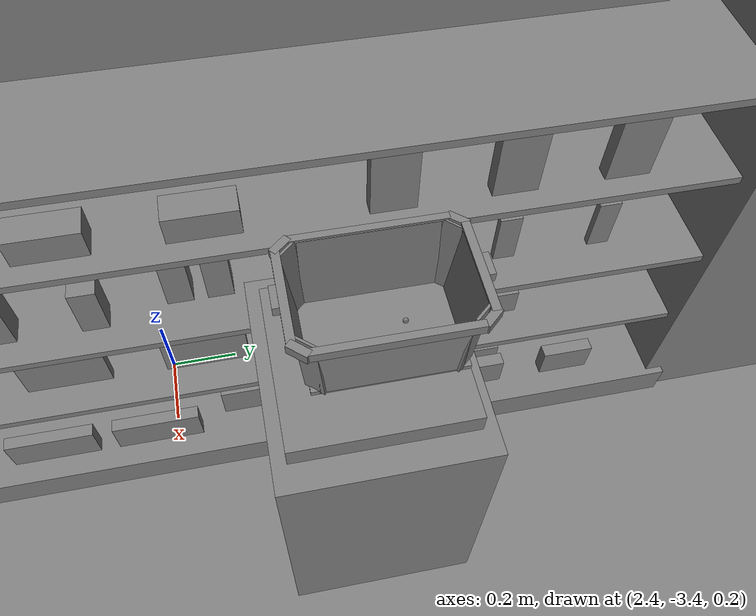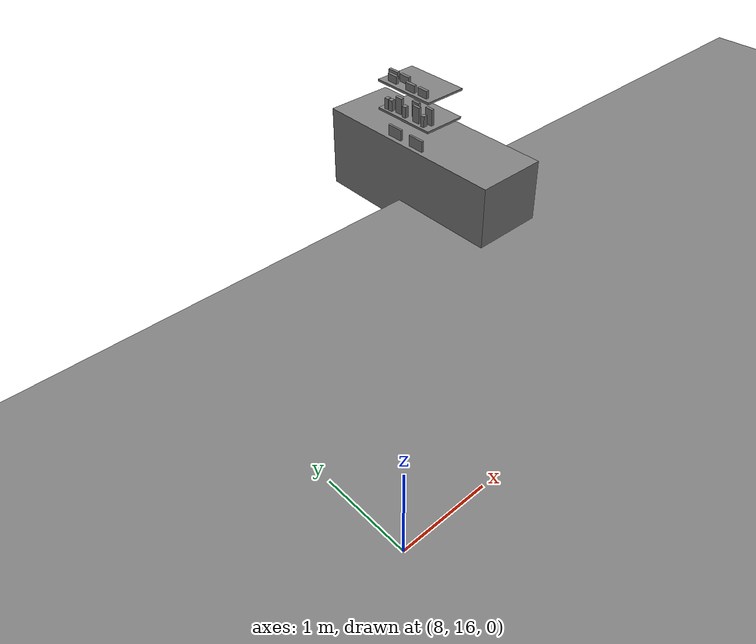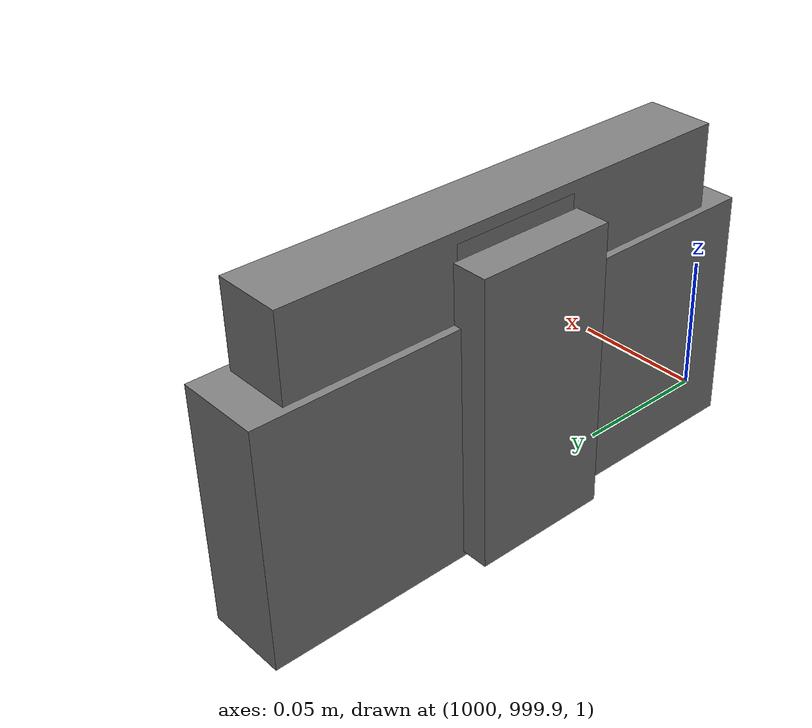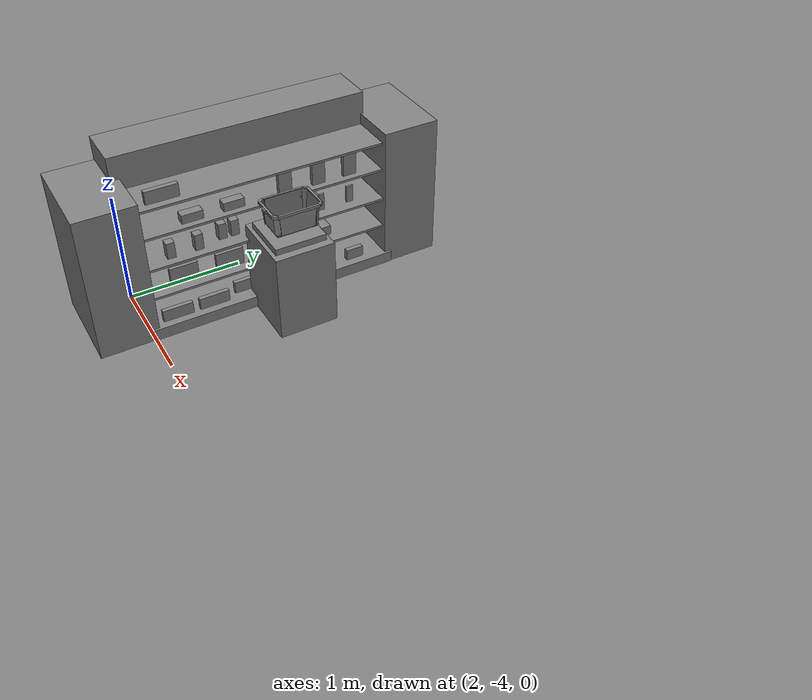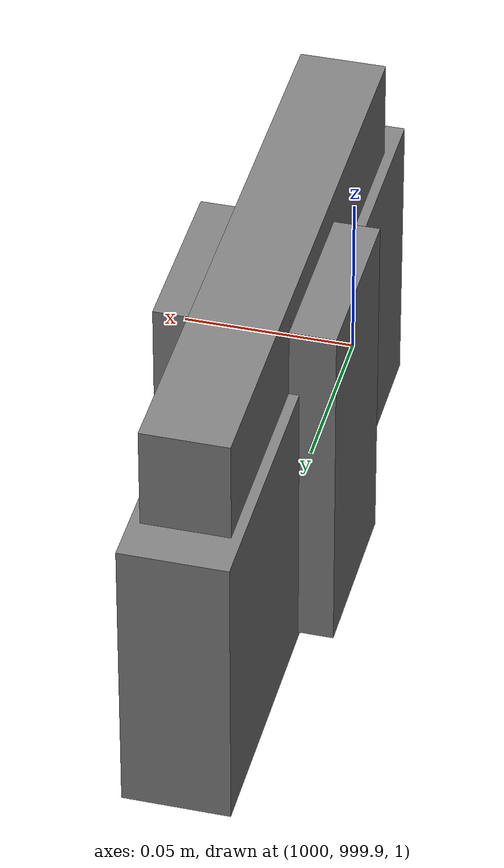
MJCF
<mujoco>
    <option gravity="0.000000000 0.000000000 -9.810000420" timestep="0.0166666" integrator="implicitfast" density="1.225" viscosity="1.8000001e-05" noslip_iterations="10" iterations="100" sdf_iterations="50">
        <flag multiccd="disable"/>
    </option>
    <size memory="1000M"/>
    <compiler coordinate="local"/>
    <worldbody>
        <light cutoff="30" pos="0 1 1" dir="0 -1 -2"/>
        <light cutoff="30" pos="0 -1 1" dir="0 1 -2"/>
        <body pos="11.742162704 20.304208755 1.369683743" euler="0.000000000 0.000000000 -85.008651733" name="openloong_gripper_2f85_fix_base_usda_jiazi_02_e_medicine_11_pz_c">
            <geom contype="1" conaffinity="1" density="1000" type="box" material="" rgba="0.500000000 0.500000000 0.500000000 1.000000000" solimp="0.899999976 0.949999988 0.001000000" friction="1.000000000 0.005000000 0.000100000" solref="0.020000000 1.000000000" margin="0" condim="3" group="0" pos="0.000000000 0.000000000 0.000000000" quat="1.000000000 0.000000000 0.000000000 0.000000000" size="0.028000001 0.029999999 0.077000000" name="openloong_gripper_2f85_fix_base_usda_jiazi_02_e_medicine_11_pz_c_C73A912F_7AC8_475C_B8E9_7041A9EA14CD"/>
            <freejoint name="openloong_gripper_2f85_fix_base_usda_jiazi_02_e_medicine_11_pz_c"/>
        </body>
        <body pos="11.742162704 19.970987320 1.373408437" euler="0.000000000 0.000000000 -85.008651733" name="openloong_gripper_2f85_fix_base_usda_jiazi_02_e_medicine_11_pz_b">
            <geom contype="1" conaffinity="1" density="1000" type="box" material="" rgba="0.500000000 0.500000000 0.500000000 1.000000000" solimp="0.899999976 0.949999988 0.001000000" friction="1.000000000 0.005000000 0.000100000" solref="0.020000000 1.000000000" margin="0" condim="3" group="0" pos="0.000000000 0.000000000 0.000000000" quat="1.000000000 0.000000000 0.000000000 0.000000000" size="0.028000001 0.029999999 0.077000000" name="openloong_gripper_2f85_fix_base_usda_jiazi_02_e_medicine_11_pz_b_EBB7FA93_A9D1_4C3F_84D0_CF38B2D0B182"/>
            <freejoint name="openloong_gripper_2f85_fix_base_usda_jiazi_02_e_medicine_11_pz_b"/>
        </body>
        <body pos="11.742162704 20.226203918 1.369683743" euler="0.000000000 0.000000000 -85.008651733" name="openloong_gripper_2f85_fix_base_usda_jiazi_02_e_medicine_11_pz_d">
            <geom contype="1" conaffinity="1" density="1000" type="box" material="" rgba="0.500000000 0.500000000 0.500000000 1.000000000" solimp="0.899999976 0.949999988 0.001000000" friction="1.000000000 0.005000000 0.000100000" solref="0.020000000 1.000000000" margin="0" condim="3" group="0" pos="0.000000000 0.000000000 0.000000000" quat="1.000000000 0.000000000 0.000000000 0.000000000" size="0.028000001 0.029999999 0.077000000" name="openloong_gripper_2f85_fix_base_usda_jiazi_02_e_medicine_11_pz_d_FE4F1FA8_1739_4DF7_ABE6_9FF104679211"/>
            <freejoint name="openloong_gripper_2f85_fix_base_usda_jiazi_02_e_medicine_11_pz_d"/>
        </body>
        <body pos="11.855587959 20.303760529 1.746467471" euler="180.000000000 0.000000000 0.000000000" name="openloong_gripper_2f85_fix_base_usda_jiazi_02_e_medicine_16_h">
            <geom contype="1" conaffinity="1" density="1000" type="box" material="" rgba="0.500000000 0.500000000 0.500000000 1.000000000" solimp="0.899999976 0.949999988 0.001000000" friction="1.000000000 0.005000000 0.000100000" solref="0.020000000 1.000000000" margin="0" condim="3" group="0" pos="0.000000000 0.000000000 0.000000000" quat="0.000000000 1.000000000 0.000000000 0.000000000" size="0.020000000 0.079000004 0.052999999" name="openloong_gripper_2f85_fix_base_usda_jiazi_02_e_medicine_16_h_C11FC041_1B0B_4C99_9FB4_6B890E2C8513"/>
            <freejoint name="openloong_gripper_2f85_fix_base_usda_jiazi_02_e_medicine_16_h"/>
        </body>
        <body pos="11.751025200 19.770164490 1.405766487" euler="0.000000000 0.000000000 0.000000000" name="openloong_gripper_2f85_fix_base_usda_jiazi_02_e_medicine_11_e">
            <geom contype="1" conaffinity="1" density="1000" type="box" material="" rgba="0.500000000 0.500000000 0.500000000 1.000000000" solimp="0.899999976 0.949999988 0.001000000" friction="1.000000000 0.005000000 0.000100000" solref="0.020000000 1.000000000" margin="0" condim="3" group="0" pos="0.000000000 0.000000000 0.000000000" quat="1.000000000 0.000000000 0.000000000 0.000000000" size="0.020000000 0.057999998 0.112999998" name="openloong_gripper_2f85_fix_base_usda_jiazi_02_e_medicine_11_e_4C920B0A_F3CA_4A23_BB38_1AEC25DF4AD3"/>
            <freejoint name="openloong_gripper_2f85_fix_base_usda_jiazi_02_e_medicine_11_e"/>
        </body>
        <body pos="2.535823345 -3.535886526 1.006494284" euler="0.000000000 0.000000000 0.000000000" name="openloong_gripper_2f85_fix_base_usda_jiazi_02_e_medicine_01_a">
            <geom contype="1" conaffinity="1" density="1000" type="box" material="" rgba="0.500000000 0.500000000 0.500000000 1.000000000" solimp="0.899999976 0.949999988 0.001000000" friction="1.000000000 0.005000000 0.000100000" solref="0.020000000 1.000000000" margin="0" condim="3" group="0" pos="0.000000000 0.000000000 0.000000000" quat="1.000000000 0.000000000 0.000000000 0.000000000" size="0.039999999 0.090000004 0.039999999" name="openloong_gripper_2f85_fix_base_usda_jiazi_02_e_medicine_01_a_90017F4B_D1FD_430E_A7D2_C1D7FD103F4A"/>
            <freejoint name="openloong_gripper_2f85_fix_base_usda_jiazi_02_e_medicine_01_a"/>
        </body>
        <body pos="11.758296013 20.215833664 1.746467471" euler="180.000000000 0.000000000 0.000000000" name="openloong_gripper_2f85_fix_base_usda_jiazi_02_e_medicine_16_e">
            <geom contype="1" conaffinity="1" density="1000" type="box" material="" rgba="0.500000000 0.500000000 0.500000000 1.000000000" solimp="0.899999976 0.949999988 0.001000000" friction="1.000000000 0.005000000 0.000100000" solref="0.020000000 1.000000000" margin="0" condim="3" group="0" pos="0.000000000 0.000000000 0.000000000" quat="0.000000000 1.000000000 0.000000000 0.000000000" size="0.020000000 0.079000004 0.052999999" name="openloong_gripper_2f85_fix_base_usda_jiazi_02_e_medicine_16_e_1DC72C49_A1E3_40AD_88F9_0A77EE6BABEF"/>
            <freejoint name="openloong_gripper_2f85_fix_base_usda_jiazi_02_e_medicine_16_e"/>
        </body>
        <body pos="2.543471813 -3.745966911 0.763295174" euler="0.000000000 0.000000000 0.000000000" name="openloong_gripper_2f85_fix_base_usda_jiazi_02_e_medicine_03_a">
            <geom contype="1" conaffinity="1" density="1000" type="box" material="" rgba="0.500000000 0.500000000 0.500000000 1.000000000" solimp="0.899999976 0.949999988 0.001000000" friction="1.000000000 0.005000000 0.000100000" solref="0.020000000 1.000000000" margin="0" condim="3" group="0" pos="0.000000000 0.000000000 0.000000000" quat="1.000000000 0.000000000 0.000000000 0.000000000" size="0.035000000 0.035000000 0.071999997" name="openloong_gripper_2f85_fix_base_usda_jiazi_02_e_medicine_03_a_E5F290E1_F8B2_4588_A631_99C97697574A"/>
            <freejoint name="openloong_gripper_2f85_fix_base_usda_jiazi_02_e_medicine_03_a"/>
        </body>
        <body pos="2.540974617 -2.634179592 0.767729700" euler="0.000000000 0.000000000 0.000000000" name="openloong_gripper_2f85_fix_base_usda_jiazi_02_e_medicine_08_b">
            <geom contype="1" conaffinity="1" density="1000" type="box" material="" rgba="0.500000000 0.500000000 0.500000000 1.000000000" solimp="0.899999976 0.949999988 0.001000000" friction="1.000000000 0.005000000 0.000100000" solref="0.020000000 1.000000000" margin="0" condim="3" group="0" pos="0.000000000 0.000000000 0.000000000" quat="1.000000000 0.000000000 0.000000000 0.000000000" size="0.010000000 0.029999999 0.075999998" name="openloong_gripper_2f85_fix_base_usda_jiazi_02_e_medicine_08_b_1B234D98_A759_4F4C_80C1_9737770F97E9"/>
            <freejoint name="openloong_gripper_2f85_fix_base_usda_jiazi_02_e_medicine_08_b"/>
        </body>
        <body pos="2.478220224 -2.398950338 0.458167851" euler="0.000000000 0.000000000 0.000000000" name="openloong_gripper_2f85_fix_base_usda_jiazi_02_e_medicine_13_b">
            <geom contype="1" conaffinity="1" density="1000" type="box" material="" rgba="0.500000000 0.500000000 0.500000000 1.000000000" solimp="0.899999976 0.949999988 0.001000000" friction="1.000000000 0.005000000 0.000100000" solref="0.020000000 1.000000000" margin="0" condim="3" group="0" pos="0.000000000 0.000000000 0.000000000" quat="1.000000000 0.000000000 0.000000000 0.000000000" size="0.067000002 0.068000004 0.044000000" name="openloong_gripper_2f85_fix_base_usda_jiazi_02_e_medicine_13_b_26B67C8B_59BF_444C_9450_8F2EF8576946"/>
            <freejoint name="openloong_gripper_2f85_fix_base_usda_jiazi_02_e_medicine_13_b"/>
        </body>
        <body pos="2.546508551 -2.439894676 0.193254441" euler="0.000000000 0.000000000 0.000000000" name="openloong_gripper_2f85_fix_base_usda_jiazi_02_e_medicine_16_a">
            <geom contype="1" conaffinity="1" density="1000" type="box" material="" rgba="0.500000000 0.500000000 0.500000000 1.000000000" solimp="0.899999976 0.949999988 0.001000000" friction="1.000000000 0.005000000 0.000100000" solref="0.020000000 1.000000000" margin="0" condim="3" group="0" pos="0.000000000 0.000000000 0.000000000" quat="1.000000000 0.000000000 0.000000000 0.000000000" size="0.020000000 0.079000004 0.052999999" name="openloong_gripper_2f85_fix_base_usda_jiazi_02_e_medicine_16_a_500BEB47_662B_4977_861F_C3F8F791F67C"/>
            <freejoint name="openloong_gripper_2f85_fix_base_usda_jiazi_02_e_medicine_16_a"/>
        </body>
        <body pos="11.743835449 19.873136520 1.746467471" euler="180.000000000 0.000000000 0.000000000" name="openloong_gripper_2f85_fix_base_usda_jiazi_02_e_medicine_16_f">
            <geom contype="1" conaffinity="1" density="1000" type="box" material="" rgba="0.500000000 0.500000000 0.500000000 1.000000000" solimp="0.899999976 0.949999988 0.001000000" friction="1.000000000 0.005000000 0.000100000" solref="0.020000000 1.000000000" margin="0" condim="3" group="0" pos="0.000000000 0.000000000 0.000000000" quat="0.000000000 1.000000000 0.000000000 0.000000000" size="0.020000000 0.079000004 0.052999999" name="openloong_gripper_2f85_fix_base_usda_jiazi_02_e_medicine_16_f_34ABA638_F874_4827_9915_9284FA6154FE"/>
            <freejoint name="openloong_gripper_2f85_fix_base_usda_jiazi_02_e_medicine_16_f"/>
        </body>
        <body pos="2.619754076 -2.721762657 0.193254441" euler="0.000000000 0.000000000 0.000000000" name="openloong_gripper_2f85_fix_base_usda_jiazi_02_e_medicine_16_d">
            <geom contype="1" conaffinity="1" density="1000" type="box" material="" rgba="0.500000000 0.500000000 0.500000000 1.000000000" solimp="0.899999976 0.949999988 0.001000000" friction="1.000000000 0.005000000 0.000100000" solref="0.020000000 1.000000000" margin="0" condim="3" group="0" pos="0.000000000 0.000000000 0.000000000" quat="1.000000000 0.000000000 0.000000000 0.000000000" size="0.020000000 0.079000004 0.052999999" name="openloong_gripper_2f85_fix_base_usda_jiazi_02_e_medicine_16_d_B237EDA8_D405_4FE8_A181_40632D408745"/>
            <freejoint name="openloong_gripper_2f85_fix_base_usda_jiazi_02_e_medicine_16_d"/>
        </body>
        <body pos="11.751626015 20.166509628 0.987222910" euler="0.000000000 0.000000000 0.000000000" name="openloong_gripper_2f85_fix_base_usda_jiazi_02_e_medicine_10_c">
            <geom contype="1" conaffinity="1" density="1000" type="box" material="" rgba="0.500000000 0.500000000 0.500000000 1.000000000" solimp="0.899999976 0.949999988 0.001000000" friction="1.000000000 0.005000000 0.000100000" solref="0.020000000 1.000000000" margin="0" condim="3" group="0" pos="0.000000000 0.000000000 0.000000000" quat="1.000000000 0.000000000 0.000000000 0.000000000" size="0.015000000 0.119999997 0.079000004" name="openloong_gripper_2f85_fix_base_usda_jiazi_02_e_medicine_10_c_47E8B680_7324_4590_8980_D0247A991C69"/>
            <freejoint name="openloong_gripper_2f85_fix_base_usda_jiazi_02_e_medicine_10_c"/>
        </body>
        <body pos="2.527985811 -2.715100288 0.458167851" euler="0.000000000 0.000000000 0.000000000" name="openloong_gripper_2f85_fix_base_usda_jiazi_02_e_medicine_13_a">
            <geom contype="1" conaffinity="1" density="1000" type="box" material="" rgba="0.500000000 0.500000000 0.500000000 1.000000000" solimp="0.899999976 0.949999988 0.001000000" friction="1.000000000 0.005000000 0.000100000" solref="0.020000000 1.000000000" margin="0" condim="3" group="0" pos="0.000000000 0.000000000 0.000000000" quat="1.000000000 0.000000000 0.000000000 0.000000000" size="0.067000002 0.068000004 0.044000000" name="openloong_gripper_2f85_fix_base_usda_jiazi_02_e_medicine_13_a_6FBB29E1_75A7_4E47_9C1C_E89107260F43"/>
            <freejoint name="openloong_gripper_2f85_fix_base_usda_jiazi_02_e_medicine_13_a"/>
        </body>
        <body pos="2.555686235 -2.149417400 1.079351544" euler="0.000000000 0.000000000 0.000000000" name="openloong_gripper_2f85_fix_base_usda_jiazi_02_e_medicine_11_b">
            <geom contype="1" conaffinity="1" density="1000" type="box" material="" rgba="0.500000000 0.500000000 0.500000000 1.000000000" solimp="0.899999976 0.949999988 0.001000000" friction="1.000000000 0.005000000 0.000100000" solref="0.020000000 1.000000000" margin="0" condim="3" group="0" pos="0.000000000 0.000000000 0.000000000" quat="1.000000000 0.000000000 0.000000000 0.000000000" size="0.020000000 0.057999998 0.112999998" name="openloong_gripper_2f85_fix_base_usda_jiazi_02_e_medicine_11_b_E6B8A595_BF1F_475F_B0E2_526A25AC7BC0"/>
            <freejoint name="openloong_gripper_2f85_fix_base_usda_jiazi_02_e_medicine_11_b"/>
        </body>
        <body pos="2.540974617 -2.413386345 0.767729700" euler="0.000000000 0.000000000 0.000000000" name="openloong_gripper_2f85_fix_base_usda_jiazi_02_e_medicine_08_c">
            <geom contype="1" conaffinity="1" density="1000" type="box" material="" rgba="0.500000000 0.500000000 0.500000000 1.000000000" solimp="0.899999976 0.949999988 0.001000000" friction="1.000000000 0.005000000 0.000100000" solref="0.020000000 1.000000000" margin="0" condim="3" group="0" pos="0.000000000 0.000000000 0.000000000" quat="1.000000000 0.000000000 0.000000000 0.000000000" size="0.010000000 0.029999999 0.075999998" name="openloong_gripper_2f85_fix_base_usda_jiazi_02_e_medicine_08_c_09E78911_A0C9_48D6_B773_BECECA673A60"/>
            <freejoint name="openloong_gripper_2f85_fix_base_usda_jiazi_02_e_medicine_08_c"/>
        </body>
        <body pos="2.497505903 -3.185120821 0.763295174" euler="0.000000000 0.000000000 0.000000000" name="openloong_gripper_2f85_fix_base_usda_jiazi_02_e_medicine_03_d">
            <geom contype="1" conaffinity="1" density="1000" type="box" material="" rgba="0.500000000 0.500000000 0.500000000 1.000000000" solimp="0.899999976 0.949999988 0.001000000" friction="1.000000000 0.005000000 0.000100000" solref="0.020000000 1.000000000" margin="0" condim="3" group="0" pos="0.000000000 0.000000000 0.000000000" quat="1.000000000 0.000000000 0.000000000 0.000000000" size="0.035000000 0.035000000 0.071999997" name="openloong_gripper_2f85_fix_base_usda_jiazi_02_e_medicine_03_d_331DA1BF_F4F1_43C3_97DE_576661C96F41"/>
            <freejoint name="openloong_gripper_2f85_fix_base_usda_jiazi_02_e_medicine_03_d"/>
        </body>
        <body pos="0.000000000 0.000000000 0.000000000" euler="0.000000000 0.000000000 0.000000000" name="Interactive Objcets_Interactive Objcets"/>
        <body pos="0.000000000 0.000000000 0.000000000" euler="0.000000000 0.000000000 0.000000000" name="Static Objcets_Static Objcets">
            <geom contype="1" conaffinity="1" density="1000" type="box" material="" rgba="0.500000000 0.500000000 0.500000000 1.000000000" solimp="0.899999976 0.959999979 0.001000000" friction="1.000000000 0.005000000 0.000100000" solref="0.020000000 1.000000000" margin="0" condim="3" group="0" pos="11.976007462 19.948400497 1.278063059" quat="1.000000000 0.000000000 0.000000000 0.000000000" size="0.300000012 0.460000008 0.015000000" name="Static Objcets_SM_guizi_06_b_C1502D27_58E0_4265_989C_2F21C2BCD5F8"/>
            <geom contype="1" conaffinity="1" density="1000" type="box" material="" rgba="0.500000000 0.500000000 0.500000000 1.000000000" solimp="0.899999976 0.959999979 0.001000000" friction="1.000000000 0.005000000 0.000100000" solref="0.020000000 1.000000000" margin="0" condim="3" group="0" pos="2.506457806 -2.919259548 0.097404450" quat="1.000000000 0.000000000 0.000000000 0.000000000" size="0.200000003 1.100000024 0.050000001" name="Static Objcets_SM_jiazi_02_h_5EC9859C_0308_44A1_BFD5_AFF7625C6DDA"/>
            <geom contype="1" conaffinity="1" density="1000" type="box" material="" rgba="0.500000000 0.500000000 0.500000000 1.000000000" solimp="0.899999976 0.959999979 0.001000000" friction="1.000000000 0.005000000 0.000100000" solref="0.020000000 1.000000000" margin="0" condim="3" group="0" pos="2.433294058 -2.920555353 0.961130261" quat="1.000000000 0.000000000 0.000000000 0.000000000" size="0.200000003 1.100000024 0.010000000" name="Static Objcets_SM_jiazi_02_e_4ECB114E_55B5_4D59_807C_EF2DFE86B843"/>
            <geom contype="1" conaffinity="1" density="1000" type="box" material="" rgba="0.500000000 0.500000000 0.500000000 1.000000000" solimp="0.899999976 0.959999979 0.001000000" friction="1.000000000 0.005000000 0.000100000" solref="0.020000000 1.000000000" margin="0" condim="3" group="0" pos="11.976007462 19.950820923 1.679351807" quat="1.000000000 0.000000000 0.000000000 0.000000000" size="0.300000012 0.460000008 0.015000000" name="Static Objcets_SM_guizi_06_c_48B1574D_F7CD_4827_997C_43DDE7599FE1"/>
            <geom contype="1" conaffinity="1" density="1000" type="box" material="" rgba="0.500000000 0.500000000 0.500000000 1.000000000" solimp="0.899999976 0.959999979 0.001000000" friction="1.000000000 0.005000000 0.000100000" solref="0.020000000 1.000000000" margin="0" condim="3" group="0" pos="12.172613144 19.933198929 0.307627976" quat="1.000000000 0.000000000 0.000000000 0.000000000" size="0.500000000 1.450000048 0.600000024" name="Static Objcets_SM_guizi_06_a_E9858B5E_F84E_4110_AACB_9653532FED53"/>
            <geom contype="1" conaffinity="1" density="1000" type="box" material="" rgba="0.500000000 0.500000000 0.500000000 1.000000000" solimp="0.899999976 0.959999979 0.001000000" friction="1.000000000 0.005000000 0.000100000" solref="0.020000000 1.000000000" margin="0" condim="3" group="0" pos="2.452836037 -2.920555353 0.682593882" quat="1.000000000 0.000000000 0.000000000 0.000000000" size="0.200000003 1.100000024 0.010000000" name="Static Objcets_SM_jiazi_02_f_CA43B461_E9E0_4352_A55A_41BE549352F5"/>
            <geom contype="1" conaffinity="1" density="1000" type="box" material="" rgba="0.500000000 0.500000000 0.500000000 1.000000000" solimp="0.899999976 0.949999988 0.001000000" friction="1.000000000 0.005000000 0.000100000" solref="0.020000000 1.000000000" margin="0" condim="3" group="0" pos="2.285422325 -4.217127323 0.670601368" quat="1.000000000 0.000000000 0.000000000 0.000000000" size="0.400000006 0.250000000 0.649999976" name="Static Objcets_SM_jiazi_02_b_CEFA52BF_456E_4D7C_81BC_B0A3D4323906"/>
            <geom contype="1" conaffinity="1" density="1000" type="box" material="" rgba="0.500000000 0.500000000 0.500000000 1.000000000" solimp="0.899999976 0.949999988 0.001000000" friction="1.000000000 0.005000000 0.000100000" solref="0.020000000 1.000000000" margin="0" condim="3" group="0" pos="2.064697266 -2.945113420 0.768164337" quat="1.000000000 0.000000000 0.000000000 0.000000000" size="0.200000003 1.100000024 0.750000000" name="Static Objcets_SM_jiazi_02_c_CC70E41A_86D3_492D_A431_FAA6A640A2D4"/>
            <geom contype="1" conaffinity="1" density="1000" type="box" material="" rgba="0.500000000 0.500000000 0.500000000 1.000000000" solimp="0.899999976 0.959999979 0.001000000" friction="1.000000000 0.005000000 0.000100000" solref="0.020000000 1.000000000" margin="0" condim="3" group="0" pos="2.437276840 -2.920555353 1.214537978" quat="1.000000000 0.000000000 0.000000000 0.000000000" size="0.200000003 1.100000024 0.010000000" name="Static Objcets_SM_jiazi_02_d_E385CDC4_E222_4FF2_B23B_5C4DA7FF62C8"/>
            <geom contype="1" conaffinity="1" density="1000" type="box" material="" rgba="0.500000000 0.500000000 0.500000000 1.000000000" solimp="0.899999976 0.959999979 0.001000000" friction="1.000000000 0.005000000 0.000100000" solref="0.020000000 1.000000000" margin="0" condim="3" group="0" pos="2.448674917 -2.920555353 0.406362146" quat="1.000000000 0.000000000 0.000000000 0.000000000" size="0.200000003 1.100000024 0.010000000" name="Static Objcets_SM_jiazi_02_g_34C64A50_9580_46B3_8244_945B678147DD"/>
            <geom contype="1" conaffinity="1" density="1000" type="plane" material="" rgba="0.500000000 0.500000000 0.500000000 1.000000000" solimp="0.899999976 0.949999988 0.001000000" friction="1.000000000 0.005000000 0.000100000" solref="0.020000000 1.000000000" margin="0" condim="3" group="0" pos="0.000000000 0.000000000 0.042896956" quat="1.000000000 0.000000000 0.000000000 0.000000000" size="20.000000000 20.000000000 1.000000000" name="Static Objcets_floor_AC58F1A2_E0B7_4E45_9223_F9C649A2470E"/>
            <geom contype="1" conaffinity="1" density="1000" type="box" material="" rgba="0.500000000 0.500000000 0.500000000 1.000000000" solimp="0.899999976 0.949999988 0.001000000" friction="1.000000000 0.005000000 0.000100000" solref="0.020000000 1.000000000" margin="0" condim="3" group="0" pos="2.285422325 -1.621193886 0.671916366" quat="1.000000000 0.000000000 0.000000000 0.000000000" size="0.400000006 0.250000000 0.649999976" name="Static Objcets_SM_jiazi_02_a_0A7DBE40_1A00_47AA_BE35_86611EE0C129"/>
        </body>
        <body pos="1000.000000000 1000.000000000 1.000000000" euler="0.000000000 0.000000000 0.000000000" name="openloong_gripper_2f85_fix_base_usda_pipalu">
            <geom contype="1" conaffinity="1" density="1000" type="box" material="" rgba="0.500000000 0.500000000 0.500000000 1.000000000" solimp="0.899999976 0.949999988 0.001000000" friction="1.000000000 0.005000000 0.000100000" solref="0.020000000 1.000000000" margin="0" condim="3" group="0" mass="0.5" pos="0.000000000 0.000000000 0.053639743" quat="1.000000000 0.000000000 0.000000000 0.000000000" size="0.011900000 0.023100000 0.053900000" name="openloong_gripper_2f85_fix_base_usda_jiazi_02_e_medicine_08_a_1D0F68CB_7A4B_4099_8B66_E5DCAA1DE18E"/>
            <freejoint name="openloong_gripper_2f85_fix_base_usda_pipalu_joint"/>
            <site size="0.005000000 0.005000000 0.005000000" rgba="0.500000000 0.500000000 0.500000000 1.000000000" pos="0.000000000 0.000000000 0.000000000" quat="0.999961913 0.008726534 0.000000000 0.000000000" group="0" type="sphere" name="openloong_gripper_2f85_fix_base_usda_pipalusite"/>
        </body>
        <body pos="2.507690430 -2.641602278 1.444427967" euler="176.980239868 31.205753326 153.230728149" mocap="true" name="spotlight2_SpotLight"/>
        <body pos="3.088733435 -2.964453936 1.467188001" euler="4.181370258 -71.456550598 -116.443595886" mocap="true" name="spotlight5_SpotLight"/>
        <body pos="1000.000000000 1000.000000000 1.000000000" euler="0.000000000 0.000000000 0.000000000" name="openloong_gripper_2f85_fix_base_usda_niuhuangwan">
            <geom contype="1" conaffinity="1" density="1000" type="box" material="" rgba="0.500000000 0.500000000 0.500000000 1.000000000" solimp="0.899999976 0.949999988 0.001000000" friction="1.000000000 0.005000000 0.000100000" solref="0.020000000 1.000000000" margin="0" condim="3" group="0" mass="0.5" pos="0.000000000 0.000000000 0.040254507" quat="1.000000000 0.000000000 0.000000000 0.000000000" size="0.014699999 0.096599996 0.041999999" name="openloong_gripper_2f85_fix_base_usda_niuhuangwan_FC23F720_21AB_4239_9A30_A1A5121A8380"/>
            <freejoint name="openloong_gripper_2f85_fix_base_usda_niuhuangwan_joint"/>
            <site size="0.005000000 0.005000000 0.005000000" rgba="0.500000000 0.500000000 0.500000000 1.000000000" pos="0.000000000 0.000000000 0.000000000" quat="0.999961913 0.008726500 0.000000000 0.000000000" group="0" type="sphere" name="openloong_gripper_2f85_fix_base_usda_niuhuangwansite"/>
        </body>
        <body pos="3.084997892 -2.779116631 1.489036918" euler="-129.981109619 46.180694580 -74.370864868" mocap="true" name="spotlight1_SpotLight"/>
        <body pos="1000.000000000 1000.000000000 1.000000000" euler="0.000000000 0.000000000 0.000000000" name="openloong_gripper_2f85_fix_base_usda_qinghuopian">
            <geom contype="1" conaffinity="1" density="1000" type="box" material="" rgba="0.500000000 0.500000000 0.500000000 1.000000000" solimp="0.899999976 0.949999988 0.001000000" friction="1.000000000 0.005000000 0.000100000" solref="0.020000000 1.000000000" margin="0" condim="3" group="0" mass="0.5" pos="0.000000000 0.000000000 0.036895368" quat="1.000000000 0.000000000 0.000000000 0.000000000" size="0.014000000 0.055300001 0.037099998" name="openloong_gripper_2f85_fix_base_usda_jiazi_02_e_medicine_16_b_4C2A738F_6DB6_4659_A7F1_783A71D2DACC"/>
            <freejoint name="openloong_gripper_2f85_fix_base_usda_qinghuopian_joint"/>
            <site size="0.005000000 0.005000000 0.005000000" rgba="0.500000000 0.500000000 0.500000000 1.000000000" pos="0.000000000 0.000000000 0.000000000" quat="0.999961913 0.008726534 0.000000000 0.000000000" group="0" type="sphere" name="openloong_gripper_2f85_fix_base_usda_qinghuopiansite"/>
        </body>
        <body pos="1000.000000000 1000.000000000 1.000000000" euler="0.000000000 0.000000000 0.000000000" name="openloong_gripper_2f85_fix_base_usda_xiaokepian">
            <geom contype="1" conaffinity="1" density="1000" type="box" material="" rgba="0.500000000 0.500000000 0.500000000 1.000000000" solimp="0.899999976 0.949999988 0.001000000" friction="1.000000000 0.005000000 0.000100000" solref="0.020000000 1.000000000" margin="0" condim="3" group="0" mass="0.5" pos="0.000000000 0.000000000 0.055557761" quat="1.000000000 0.000000000 0.000000000 0.000000000" size="0.011900000 0.083999999 0.055999998" name="openloong_gripper_2f85_fix_base_usda_jiazi_02_e_medicine_10_a_FF2089F7_58B5_4B04_9BBB_7E1878795053"/>
            <freejoint name="openloong_gripper_2f85_fix_base_usda_xiaokepian_joint"/>
            <site size="0.005000000 0.005000000 0.005000000" rgba="0.500000000 0.500000000 0.500000000 1.000000000" pos="0.000000000 0.000000000 0.000000000" quat="0.999961913 0.008726534 0.000000000 0.000000000" group="0" type="sphere" name="openloong_gripper_2f85_fix_base_usda_xiaokepiansite"/>
        </body>
        <body pos="1000.000000000 1000.000000000 1.000000000" euler="0.000000000 0.000000000 0.000000000" name="openloong_gripper_2f85_fix_base_usda_orangebox">
            <geom contype="1" conaffinity="1" density="1000" type="box" material="" rgba="0.500000000 0.500000000 0.500000000 1.000000000" solimp="0.899999976 0.949999988 0.001000000" friction="1.000000000 0.005000000 0.000100000" solref="0.020000000 1.000000000" margin="0" condim="3" group="0" mass="0.5" pos="0.000000000 0.000000000 0.051213536" quat="1.000000000 0.000000000 0.000000000 0.000000000" size="0.024499999 0.024499999 0.051099997" name="openloong_gripper_2f85_fix_base_usda_jiazi_02_e_medicine_03_a_EE0A441C_EC73_4E16_A66C_9A378E8C35E7"/>
            <freejoint name="openloong_gripper_2f85_fix_base_usda_orangebox_joint"/>
            <site size="0.005000000 0.005000000 0.005000000" rgba="0.500000000 0.500000000 0.500000000 1.000000000" pos="0.000000000 0.000000000 0.000000000" quat="0.999961913 0.008726535 0.000000000 0.000000000" group="0" type="sphere" name="openloong_gripper_2f85_fix_base_usda_orangeboxsite"/>
        </body>
        <body pos="2.608781099 -2.144529104 0.193254441" euler="0.000000000 0.000000000 0.000000000" name="openloong_gripper_2f85_fix_base_usda_jiazi_02_e_medicine_16_c">
            <geom contype="1" conaffinity="1" density="1000" type="box" material="" rgba="0.500000000 0.500000000 0.500000000 1.000000000" solimp="0.899999976 0.949999988 0.001000000" friction="1.000000000 0.005000000 0.000100000" solref="0.020000000 1.000000000" margin="0" condim="3" group="0" pos="0.000000000 0.000000000 0.000000000" quat="1.000000000 0.000000000 0.000000000 0.000000000" size="0.020000000 0.079000004 0.052999999" name="openloong_gripper_2f85_fix_base_usda_jiazi_02_e_medicine_16_c_751D1D13_FA0E_4E40_84E6_DF288A931B1B"/>
            <freejoint name="openloong_gripper_2f85_fix_base_usda_jiazi_02_e_medicine_16_c"/>
        </body>
        <body pos="2.877940178 -2.751950979 0.062857389" euler="0.000000000 0.000000000 0.000000000" name="[25355134294587]_DeliveryRobot_01">
            <geom contype="1" conaffinity="1" density="1000" type="box" material="" rgba="0.500000000 0.500000000 0.500000000 1.000000000" solimp="0.899999976 0.949999988 0.001000000" friction="1.000000000 0.005000000 0.000100000" solref="0.020000000 1.000000000" margin="0" condim="3" group="0" pos="0.000000000 -0.111846209 0.319800019" quat="1.000000000 0.000000000 0.000000000 0.000000000" size="0.289999992 0.254999995 0.419999987" name="[25355134294587]_geom_1E496DE0_D567_4654_840B_648C27B96F21"/>
            <geom contype="1" conaffinity="1" density="1000" type="box" material="" rgba="0.500000000 0.500000000 0.500000000 1.000000000" solimp="0.899999976 0.949999988 0.001000000" friction="1.000000000 0.005000000 0.000100000" solref="0.020000000 1.000000000" margin="0" condim="3" group="0" pos="0.000000000 -0.111846209 0.744405389" quat="1.000000000 0.000000000 0.000000000 0.000000000" size="0.219999999 0.219999999 0.050000001" name="[25355134294587]_geom_07306D29_2A31_4F9E_9AEF_E8C5AE0205DB"/>
        </body>
        <body pos="2.859023094 -2.828485012 0.874997377" euler="89.999946594 0.000000000 0.000000000" name="openloong_gripper_2f85_fix_base_usda_MedicineChest">
            <geom contype="1" conaffinity="1" density="100000" type="box" material="" rgba="0.500000000 0.500000000 0.500000000 1.000000000" solimp="0.899999976 0.949999988 0.001000000" friction="1.000000000 0.899999976 0.000100000" solref="0.020000000 1.000000000" margin="0" condim="3" group="0" pos="-0.113059282 0.107842624 0.177997828" quat="0.369108677 0.045244619 -0.928185225 -0.013556212" size="0.003000000 0.100000001 0.026000001" name="openloong_gripper_2f85_fix_base_usda_geom_A30F5BE5_A419_4C1D_8D3F_0739FFCDCEF0"/>
            <geom contype="1" conaffinity="1" density="100000" type="box" material="" rgba="0.500000000 0.500000000 0.500000000 1.000000000" solimp="0.899999976 0.949999988 0.001000000" friction="1.000000000 0.899999976 0.000100000" solref="0.020000000 1.000000000" margin="0" condim="3" group="0" pos="0.000000000 0.005823255 0.000000000" quat="1.000000000 0.000000000 0.000000000 0.000000000" size="0.122000001 0.006000000 0.180000007" name="openloong_gripper_2f85_fix_base_usda_geom_D929206A_FBCF_4D4A_8321_E6466601A946"/>
            <geom contype="1" conaffinity="1" density="100000" type="box" material="" rgba="0.500000000 0.500000000 0.500000000 1.000000000" solimp="0.899999976 0.949999988 0.001000000" friction="1.000000000 0.899999976 0.000100000" solref="0.020000000 1.000000000" margin="0" condim="3" group="0" pos="0.145289421 0.198014736 -0.000000238" quat="1.000000000 0.000000000 0.000000000 0.000000000" size="0.009000000 0.012000000 0.180000007" name="openloong_gripper_2f85_fix_base_usda_geom_BFAFEC6E_6682_40B2_BEC8_795D3A91A21A"/>
            <geom contype="1" conaffinity="1" density="100000" type="box" material="" rgba="0.500000000 0.500000000 0.500000000 1.000000000" solimp="0.899999976 0.949999988 0.001000000" friction="1.000000000 0.899999976 0.000100000" solref="0.020000000 1.000000000" margin="0" condim="3" group="0" pos="-0.116801500 0.106451452 -0.175024986" quat="-0.356188178 0.039200634 -0.932773709 0.039071620" size="0.003000000 0.100000001 0.026000001" name="openloong_gripper_2f85_fix_base_usda_geom_5A81D872_670F_4989_89A6_7652A6BF451F"/>
            <geom contype="1" conaffinity="1" density="100000" type="box" material="" rgba="0.500000000 0.500000000 0.500000000 1.000000000" solimp="0.899999976 0.949999988 0.001000000" friction="1.000000000 0.899999976 0.000100000" solref="0.020000000 1.000000000" margin="0" condim="3" group="0" pos="-0.000797749 0.196027160 0.223680258" quat="0.707158327 -0.000001520 0.707055092 -0.000001520" size="0.010000000 0.012000000 0.029999999" name="openloong_gripper_2f85_fix_base_usda_geom_30427F0D_763D_40AE_BAC5_2FC66CB27615"/>
            <geom contype="1" conaffinity="1" density="100000" type="box" material="" rgba="0.500000000 0.500000000 0.500000000 1.000000000" solimp="0.899999976 0.949999988 0.001000000" friction="1.000000000 0.899999976 0.000100000" solref="0.020000000 1.000000000" margin="0" condim="3" group="0" pos="0.128487587 0.105749547 0.000000238" quat="0.999090791 0.000000030 -0.000000002 -0.042632505" size="0.003000000 0.100000001 0.159999996" name="openloong_gripper_2f85_fix_base_usda_geom_14D635DB_839A_4720_A997_6DF27F801163"/>
            <geom contype="1" conaffinity="1" density="100000" type="box" material="" rgba="0.500000000 0.500000000 0.500000000 1.000000000" solimp="0.899999976 0.949999988 0.001000000" friction="1.000000000 0.899999976 0.000100000" solref="0.020000000 1.000000000" margin="0" condim="3" group="0" pos="-0.132964611 0.198016286 0.194559574" quat="0.359685898 -0.000000596 -0.933073401 0.000003695" size="0.010000000 0.012000000 0.026000001" name="openloong_gripper_2f85_fix_base_usda_geom_E348F34B_6CC3_416A_A5D8_F1223E2EB8F5"/>
            <geom contype="1" conaffinity="1" density="100000" type="box" material="" rgba="0.500000000 0.500000000 0.500000000 1.000000000" solimp="0.899999976 0.949999988 0.001000000" friction="1.000000000 0.899999976 0.000100000" solref="0.020000000 1.000000000" margin="0" condim="3" group="0" pos="0.000000715 0.198014379 0.208025932" quat="0.707159519 -0.000000089 0.707053959 -0.000000060" size="0.010000000 0.012000000 0.119999997" name="openloong_gripper_2f85_fix_base_usda_geom_74C8D0D7_EAC5_41A3_AA7A_A3A2D0A15AF0"/>
            <geom contype="1" conaffinity="1" density="100000" type="box" material="" rgba="0.500000000 0.500000000 0.500000000 1.000000000" solimp="0.899999976 0.949999988 0.001000000" friction="1.000000000 0.899999976 0.000100000" solref="0.020000000 1.000000000" margin="0" condim="3" group="0" pos="0.115736485 0.109648407 -0.172922373" quat="-0.356657803 0.026131347 0.933247149 -0.034088194" size="0.003000000 0.100000001 0.026000001" name="openloong_gripper_2f85_fix_base_usda_geom_19DA56A1_09E5_4600_A534_DF516B2009AB"/>
            <geom contype="1" conaffinity="1" density="100000" type="box" material="" rgba="0.500000000 0.500000000 0.500000000 1.000000000" solimp="0.899999976 0.949999988 0.001000000" friction="1.000000000 0.899999976 0.000100000" solref="0.020000000 1.000000000" margin="0" condim="3" group="0" pos="0.000526667 0.104760587 -0.187798262" quat="0.705659389 -0.045368463 0.705640316 -0.045367181" size="0.003000000 0.100000001 0.100000001" name="openloong_gripper_2f85_fix_base_usda_geom_90C1533F_BA41_4F06_B107_F6DB92E3039B"/>
            <geom contype="1" conaffinity="1" density="100000" type="box" material="" rgba="0.500000000 0.500000000 0.500000000 1.000000000" solimp="0.899999976 0.949999988 0.001000000" friction="1.000000000 0.899999976 0.000100000" solref="0.020000000 1.000000000" margin="0" condim="3" group="0" pos="-0.000797749 0.196027160 -0.223680258" quat="0.707158327 -0.000001520 0.707055092 -0.000001520" size="0.010000000 0.012000000 0.029999999" name="openloong_gripper_2f85_fix_base_usda_geom_192F6B51_406E_4E1A_B522_43C44C5B0E05"/>
            <geom contype="1" conaffinity="1" density="100000" type="box" material="" rgba="0.500000000 0.500000000 0.500000000 1.000000000" solimp="0.899999976 0.949999988 0.001000000" friction="1.000000000 0.899999976 0.000100000" solref="0.020000000 1.000000000" margin="0" condim="3" group="0" pos="0.115026236 0.107592762 0.174144983" quat="0.930772185 0.025311798 -0.363503337 -0.029796928" size="0.003000000 0.100000001 0.026000001" name="openloong_gripper_2f85_fix_base_usda_geom_A757FBB8_017F_4847_8103_449F9439B08F"/>
            <geom contype="1" conaffinity="1" density="100000" type="box" material="" rgba="0.500000000 0.500000000 0.500000000 1.000000000" solimp="0.899999976 0.949999988 0.001000000" friction="1.000000000 0.899999976 0.000100000" solref="0.020000000 1.000000000" margin="0" condim="3" group="0" pos="0.000000715 0.198014379 -0.208025932" quat="0.707159519 -0.000000089 0.707053959 -0.000000060" size="0.010000000 0.012000000 0.119999997" name="openloong_gripper_2f85_fix_base_usda_geom_4BB8A44A_0D13_4A88_9EC2_BAA0E012EA14"/>
            <geom contype="1" conaffinity="1" density="100000" type="box" material="" rgba="0.500000000 0.500000000 0.500000000 1.000000000" solimp="0.899999976 0.949999988 0.001000000" friction="1.000000000 0.899999976 0.000100000" solref="0.020000000 1.000000000" margin="0" condim="3" group="0" pos="-0.145288944 0.198014736 -0.000000238" quat="1.000000000 0.000000000 0.000000000 0.000000000" size="0.009000000 0.012000000 0.180000007" name="openloong_gripper_2f85_fix_base_usda_geom_495026D7_C997_4231_BF56_A545D7828B75"/>
            <geom contype="1" conaffinity="1" density="100000" type="box" material="" rgba="0.500000000 0.500000000 0.500000000 1.000000000" solimp="0.899999976 0.949999988 0.001000000" friction="1.000000000 0.899999976 0.000100000" solref="0.020000000 1.000000000" margin="0" condim="3" group="0" pos="-0.133216143 0.198014021 -0.194619179" quat="-0.359760642 0.000001267 -0.933044553 0.000001341" size="0.010000000 0.012000000 0.026000001" name="openloong_gripper_2f85_fix_base_usda_geom_8E169E0D_1631_4A1C_A2FB_A5AC084E6934"/>
            <geom contype="1" conaffinity="1" density="100000" type="box" material="" rgba="0.500000000 0.500000000 0.500000000 1.000000000" solimp="0.899999976 0.949999988 0.001000000" friction="1.000000000 0.899999976 0.000100000" solref="0.020000000 1.000000000" margin="0" condim="3" group="0" pos="-0.128487349 0.105749547 0.000000238" quat="0.999090791 0.000000030 -0.000000002 0.042632505" size="0.003000000 0.100000001 0.159999996" name="openloong_gripper_2f85_fix_base_usda_geom_93505A79_3E27_48F5_AC82_E9E343804CC5"/>
            <geom contype="1" conaffinity="1" density="100000" type="box" material="" rgba="0.500000000 0.500000000 0.500000000 1.000000000" solimp="0.899999976 0.949999988 0.001000000" friction="1.000000000 0.899999976 0.000100000" solref="0.020000000 1.000000000" margin="0" condim="3" group="0" pos="0.131582499 0.198014021 -0.194822311" quat="0.359707981 -0.000000596 -0.933064938 0.000003695" size="0.010000000 0.012000000 0.026000001" name="openloong_gripper_2f85_fix_base_usda_geom_FF7CAE20_D1BE_4484_8D24_2B71E3673D64"/>
            <geom contype="1" conaffinity="1" density="100000" type="box" material="" rgba="0.500000000 0.500000000 0.500000000 1.000000000" solimp="0.899999976 0.949999988 0.001000000" friction="1.000000000 0.899999976 0.000100000" solref="0.020000000 1.000000000" margin="0" condim="3" group="0" pos="0.132833242 0.198015213 0.194798470" quat="-0.359736264 0.000001252 -0.933053970 0.000001401" size="0.010000000 0.012000000 0.026000001" name="openloong_gripper_2f85_fix_base_usda_geom_1A7766ED_A110_48C8_8A51_679573C5D052"/>
            <geom contype="1" conaffinity="1" density="100000" type="box" material="" rgba="0.500000000 0.500000000 0.500000000 1.000000000" solimp="0.899999976 0.949999988 0.001000000" friction="1.000000000 0.899999976 0.000100000" solref="0.020000000 1.000000000" margin="0" condim="3" group="0" pos="0.000516415 0.102862239 0.189926386" quat="0.705658197 0.045368552 0.705641508 0.045367509" size="0.003000000 0.100000001 0.100000001" name="openloong_gripper_2f85_fix_base_usda_geom_312725CD_75F7_4EEA_918F_122CDA82575F"/>
            <freejoint name="openloong_gripper_2f85_fix_base_usda_MedicineChest_joint"/>
            <site size="0.005000000 0.005000000 0.005000000" rgba="0.500000000 0.500000000 0.500000000 1.000000000" pos="0.000000000 0.000000000 0.000000000" quat="1.000000000 0.000000000 0.000000000 0.000000000" group="0" type="sphere" name="openloong_gripper_2f85_fix_base_usda_MedicineChestsite"/>
        </body>
        <body pos="11.855587959 20.093915939 1.746467471" euler="180.000000000 0.000000000 0.000000000" name="openloong_gripper_2f85_fix_base_usda_jiazi_02_e_medicine_16_i">
            <geom contype="1" conaffinity="1" density="1000" type="box" material="" rgba="0.500000000 0.500000000 0.500000000 1.000000000" solimp="0.899999976 0.949999988 0.001000000" friction="1.000000000 0.005000000 0.000100000" solref="0.020000000 1.000000000" margin="0" condim="3" group="0" pos="0.000000000 0.000000000 0.000000000" quat="0.000000000 1.000000000 0.000000000 0.000000000" size="0.020000000 0.079000004 0.052999999" name="openloong_gripper_2f85_fix_base_usda_jiazi_02_e_medicine_16_i_B10750FF_16F7_4BAD_96E9_731AB23EC8C6"/>
            <freejoint name="openloong_gripper_2f85_fix_base_usda_jiazi_02_e_medicine_16_i"/>
        </body>
        <body pos="2.543471813 -3.511630297 0.763295174" euler="0.000000000 0.000000000 0.000000000" name="openloong_gripper_2f85_fix_base_usda_jiazi_02_e_medicine_03_b">
            <geom contype="1" conaffinity="1" density="1000" type="box" material="" rgba="0.500000000 0.500000000 0.500000000 1.000000000" solimp="0.899999976 0.949999988 0.001000000" friction="1.000000000 0.005000000 0.000100000" solref="0.020000000 1.000000000" margin="0" condim="3" group="0" pos="0.000000000 0.000000000 0.000000000" quat="1.000000000 0.000000000 0.000000000 0.000000000" size="0.035000000 0.035000000 0.071999997" name="openloong_gripper_2f85_fix_base_usda_jiazi_02_e_medicine_03_b_5387DC2C_74BB_4AD6_9781_1B9FDC72272F"/>
            <freejoint name="openloong_gripper_2f85_fix_base_usda_jiazi_02_e_medicine_03_b"/>
        </body>
        <body pos="11.835501671 19.621755600 1.405766487" euler="0.000000000 0.000000000 0.000000000" name="openloong_gripper_2f85_fix_base_usda_jiazi_02_e_medicine_11_g">
            <geom contype="1" conaffinity="1" density="1000" type="box" material="" rgba="0.500000000 0.500000000 0.500000000 1.000000000" solimp="0.899999976 0.949999988 0.001000000" friction="1.000000000 0.005000000 0.000100000" solref="0.020000000 1.000000000" margin="0" condim="3" group="0" pos="0.000000000 0.000000000 0.000000000" quat="1.000000000 0.000000000 0.000000000 0.000000000" size="0.020000000 0.057999998 0.112999998" name="openloong_gripper_2f85_fix_base_usda_jiazi_02_e_medicine_11_g_FB5F9BE5_3309_4938_97E2_BD6D38DCAE5B"/>
            <freejoint name="openloong_gripper_2f85_fix_base_usda_jiazi_02_e_medicine_11_g"/>
        </body>
        <body pos="2.540798664 -3.660816193 0.494465470" euler="0.000000000 0.000000000 0.000000000" name="openloong_gripper_2f85_fix_base_usda_jiazi_02_e_medicine_10_b">
            <geom contype="1" conaffinity="1" density="1000" type="box" material="" rgba="0.500000000 0.500000000 0.500000000 1.000000000" solimp="0.899999976 0.949999988 0.001000000" friction="1.000000000 0.005000000 0.000100000" solref="0.020000000 1.000000000" margin="0" condim="3" group="0" pos="0.000000000 0.000000000 0.000000000" quat="1.000000000 0.000000000 0.000000000 0.000000000" size="0.015000000 0.119999997 0.079000004" name="openloong_gripper_2f85_fix_base_usda_jiazi_02_e_medicine_10_b_9226BD21_95B8_40CF_9378_9D5C6449D5EE"/>
            <freejoint name="openloong_gripper_2f85_fix_base_usda_jiazi_02_e_medicine_10_b"/>
        </body>
        <body pos="2.555686235 -2.437009096 1.079351544" euler="0.000000000 0.000000000 0.000000000" name="openloong_gripper_2f85_fix_base_usda_jiazi_02_e_medicine_11_a">
            <geom contype="1" conaffinity="1" density="1000" type="box" material="" rgba="0.500000000 0.500000000 0.500000000 1.000000000" solimp="0.899999976 0.949999988 0.001000000" friction="1.000000000 0.005000000 0.000100000" solref="0.020000000 1.000000000" margin="0" condim="3" group="0" pos="0.000000000 0.000000000 0.000000000" quat="1.000000000 0.000000000 0.000000000 0.000000000" size="0.020000000 0.057999998 0.112999998" name="openloong_gripper_2f85_fix_base_usda_jiazi_02_e_medicine_11_a_8972E11A_21E9_4F5A_94AB_F8F0348EF6C2"/>
            <freejoint name="openloong_gripper_2f85_fix_base_usda_jiazi_02_e_medicine_11_a"/>
        </body>
        <body pos="2.547302485 -3.744830847 1.280401945" euler="0.000000000 0.000000000 0.000000000" name="openloong_gripper_2f85_fix_base_usda_jiazi_02_e_medicine_14_b">
            <geom contype="1" conaffinity="1" density="1000" type="box" material="" rgba="0.500000000 0.500000000 0.500000000 1.000000000" solimp="0.899999976 0.949999988 0.001000000" friction="1.000000000 0.005000000 0.000100000" solref="0.020000000 1.000000000" margin="0" condim="3" group="0" pos="0.000000000 0.000000000 0.000000000" quat="1.000000000 0.000000000 0.000000000 0.000000000" size="0.021000000 0.136999995 0.057000000" name="openloong_gripper_2f85_fix_base_usda_jiazi_02_e_medicine_14_b_D6ACBACD_ECC1_44F1_A2BB_EE79B4D4BD9F"/>
            <freejoint name="openloong_gripper_2f85_fix_base_usda_jiazi_02_e_medicine_14_b"/>
        </body>
        <body pos="2.608781099 -2.439894676 0.193254441" euler="0.000000000 0.000000000 0.000000000" name="openloong_gripper_2f85_fix_base_usda_jiazi_02_e_medicine_16_b">
            <geom contype="1" conaffinity="1" density="1000" type="box" material="" rgba="0.500000000 0.500000000 0.500000000 1.000000000" solimp="0.899999976 0.949999988 0.001000000" friction="1.000000000 0.005000000 0.000100000" solref="0.020000000 1.000000000" margin="0" condim="3" group="0" pos="0.000000000 0.000000000 0.000000000" quat="1.000000000 0.000000000 0.000000000 0.000000000" size="0.020000000 0.079000004 0.052999999" name="openloong_gripper_2f85_fix_base_usda_jiazi_02_e_medicine_16_b_49B8BA6E_7F20_4C2E_A329_5A763B55DAC3"/>
            <freejoint name="openloong_gripper_2f85_fix_base_usda_jiazi_02_e_medicine_16_b"/>
        </body>
        <body pos="2.540974617 -2.142210245 0.767729700" euler="0.000000000 0.000000000 0.000000000" name="openloong_gripper_2f85_fix_base_usda_jiazi_02_e_medicine_08_d">
            <geom contype="1" conaffinity="1" density="1000" type="box" material="" rgba="0.500000000 0.500000000 0.500000000 1.000000000" solimp="0.899999976 0.949999988 0.001000000" friction="1.000000000 0.005000000 0.000100000" solref="0.020000000 1.000000000" margin="0" condim="3" group="0" pos="0.000000000 0.000000000 0.000000000" quat="1.000000000 0.000000000 0.000000000 0.000000000" size="0.010000000 0.029999999 0.075999998" name="openloong_gripper_2f85_fix_base_usda_jiazi_02_e_medicine_08_d_2D3C52B8_066C_4957_ACD2_F32CF609A001"/>
            <freejoint name="openloong_gripper_2f85_fix_base_usda_jiazi_02_e_medicine_08_d"/>
        </body>
        <body pos="11.749706268 19.659208298 1.746467471" euler="180.000000000 0.000000000 0.000000000" name="openloong_gripper_2f85_fix_base_usda_jiazi_02_e_medicine_16_g">
            <geom contype="1" conaffinity="1" density="1000" type="box" material="" rgba="0.500000000 0.500000000 0.500000000 1.000000000" solimp="0.899999976 0.949999988 0.001000000" friction="1.000000000 0.005000000 0.000100000" solref="0.020000000 1.000000000" margin="0" condim="3" group="0" pos="0.000000000 0.000000000 0.000000000" quat="0.000000000 1.000000000 0.000000000 0.000000000" size="0.020000000 0.079000004 0.052999999" name="openloong_gripper_2f85_fix_base_usda_jiazi_02_e_medicine_16_g_12FFE143_9F62_4F68_A075_23AAB56605FE"/>
            <freejoint name="openloong_gripper_2f85_fix_base_usda_jiazi_02_e_medicine_16_g"/>
        </body>
        <body pos="2.617633820 -3.462228775 0.195964247" euler="0.000000000 0.000000000 0.000000000" name="openloong_gripper_2f85_fix_base_usda_jiazi_02_e_medicine_17_a">
            <geom contype="1" conaffinity="1" density="1000" type="box" material="" rgba="0.500000000 0.500000000 0.500000000 1.000000000" solimp="0.899999976 0.949999988 0.001000000" friction="1.000000000 0.005000000 0.000100000" solref="0.020000000 1.000000000" margin="0" condim="3" group="0" pos="0.000000000 0.000000000 0.000000000" quat="1.000000000 0.000000000 0.000000000 0.000000000" size="0.018999999 0.129999995 0.056000002" name="openloong_gripper_2f85_fix_base_usda_jiazi_02_e_medicine_17_a_A8709356_8FCA_4B3D_BC41_2157D6FA1086"/>
            <freejoint name="openloong_gripper_2f85_fix_base_usda_jiazi_02_e_medicine_17_a"/>
        </body>
        <body pos="2.555686235 -2.738002539 1.079351544" euler="0.000000000 0.000000000 0.000000000" name="openloong_gripper_2f85_fix_base_usda_jiazi_02_e_medicine_11_c">
            <geom contype="1" conaffinity="1" density="1000" type="box" material="" rgba="0.500000000 0.500000000 0.500000000 1.000000000" solimp="0.899999976 0.949999988 0.001000000" friction="1.000000000 0.005000000 0.000100000" solref="0.020000000 1.000000000" margin="0" condim="3" group="0" pos="0.000000000 0.000000000 0.000000000" quat="1.000000000 0.000000000 0.000000000 0.000000000" size="0.020000000 0.057999998 0.112999998" name="openloong_gripper_2f85_fix_base_usda_jiazi_02_e_medicine_11_c_506783BD_B5FD_4EDA_A600_B165F800CA07"/>
            <freejoint name="openloong_gripper_2f85_fix_base_usda_jiazi_02_e_medicine_11_c"/>
        </body>
        <body pos="11.742162704 19.632486343 1.369683743" euler="0.000000000 0.000000000 -85.008651733" name="openloong_gripper_2f85_fix_base_usda_jiazi_02_e_medicine_11_pz_a">
            <geom contype="1" conaffinity="1" density="1000" type="box" material="" rgba="0.500000000 0.500000000 0.500000000 1.000000000" solimp="0.899999976 0.949999988 0.001000000" friction="1.000000000 0.005000000 0.000100000" solref="0.020000000 1.000000000" margin="0" condim="3" group="0" pos="0.000000000 0.000000000 0.000000000" quat="1.000000000 0.000000000 0.000000000 0.000000000" size="0.028000001 0.029999999 0.077000000" name="openloong_gripper_2f85_fix_base_usda_jiazi_02_e_medicine_11_pz_a_F59E49F5_77DE_4C7E_8DA0_BA53F64F15B9"/>
            <freejoint name="openloong_gripper_2f85_fix_base_usda_jiazi_02_e_medicine_11_pz_a"/>
        </body>
        <body pos="11.746563911 19.764736176 0.987372577" euler="0.000000000 0.000000000 180.000000000" name="openloong_gripper_2f85_fix_base_usda_jiazi_02_e_medicine_10_d">
            <geom contype="1" conaffinity="1" density="1000" type="box" material="" rgba="0.500000000 0.500000000 0.500000000 1.000000000" solimp="0.899999976 0.949999988 0.001000000" friction="1.000000000 0.005000000 0.000100000" solref="0.020000000 1.000000000" margin="0" condim="3" group="0" pos="0.000000000 0.000000000 0.000000000" quat="0.000000000 0.000000000 0.000000000 -1.000000000" size="0.015000000 0.119999997 0.079000004" name="openloong_gripper_2f85_fix_base_usda_jiazi_02_e_medicine_10_d_609BA48D_FE0A_4508_83D3_6F06D5680DD1"/>
            <freejoint name="openloong_gripper_2f85_fix_base_usda_jiazi_02_e_medicine_10_d"/>
        </body>
        <body pos="2.535823345 -3.186250448 1.006494284" euler="0.000000000 0.000000000 0.000000000" name="openloong_gripper_2f85_fix_base_usda_jiazi_02_e_medicine_01_b">
            <geom contype="1" conaffinity="1" density="1000" type="box" material="" rgba="0.500000000 0.500000000 0.500000000 1.000000000" solimp="0.899999976 0.949999988 0.001000000" friction="1.000000000 0.005000000 0.000100000" solref="0.020000000 1.000000000" margin="0" condim="3" group="0" pos="0.000000000 0.000000000 0.000000000" quat="1.000000000 0.000000000 0.000000000 0.000000000" size="0.039999999 0.090000004 0.039999999" name="openloong_gripper_2f85_fix_base_usda_jiazi_02_e_medicine_01_b_B754D162_A65F_4C72_A2EA_6780E389A34F"/>
            <freejoint name="openloong_gripper_2f85_fix_base_usda_jiazi_02_e_medicine_01_b"/>
        </body>
        <body pos="2.540798664 -3.265180588 0.494465470" euler="0.000000000 0.000000000 0.000000000" name="openloong_gripper_2f85_fix_base_usda_jiazi_02_e_medicine_10_a">
            <geom contype="1" conaffinity="1" density="1000" type="box" material="" rgba="0.500000000 0.500000000 0.500000000 1.000000000" solimp="0.899999976 0.949999988 0.001000000" friction="1.000000000 0.005000000 0.000100000" solref="0.020000000 1.000000000" margin="0" condim="3" group="0" pos="0.000000000 0.000000000 0.000000000" quat="1.000000000 0.000000000 0.000000000 0.000000000" size="0.015000000 0.119999997 0.079000004" name="openloong_gripper_2f85_fix_base_usda_jiazi_02_e_medicine_10_a_476242DD_F802_4A09_80C8_6FEA50B9E38D"/>
            <freejoint name="openloong_gripper_2f85_fix_base_usda_jiazi_02_e_medicine_10_a"/>
        </body>
        <body pos="11.763878822 20.100526810 1.405766487" euler="0.000000000 0.000000000 0.000000000" name="openloong_gripper_2f85_fix_base_usda_jiazi_02_e_medicine_11_d">
            <geom contype="1" conaffinity="1" density="1000" type="box" material="" rgba="0.500000000 0.500000000 0.500000000 1.000000000" solimp="0.899999976 0.949999988 0.001000000" friction="1.000000000 0.005000000 0.000100000" solref="0.020000000 1.000000000" margin="0" condim="3" group="0" pos="0.000000000 0.000000000 0.000000000" quat="1.000000000 0.000000000 0.000000000 0.000000000" size="0.020000000 0.057999998 0.112999998" name="openloong_gripper_2f85_fix_base_usda_jiazi_02_e_medicine_11_d_5AB8314D_3CE4_45A5_B092_D48213E2A004"/>
            <freejoint name="openloong_gripper_2f85_fix_base_usda_jiazi_02_e_medicine_11_d"/>
        </body>
        <body pos="2.557055712 -3.127499342 0.195964247" euler="0.000000000 0.000000000 0.000000000" name="openloong_gripper_2f85_fix_base_usda_jiazi_02_e_medicine_17_c">
            <geom contype="1" conaffinity="1" density="1000" type="box" material="" rgba="0.500000000 0.500000000 0.500000000 1.000000000" solimp="0.899999976 0.949999988 0.001000000" friction="1.000000000 0.005000000 0.000100000" solref="0.020000000 1.000000000" margin="0" condim="3" group="0" pos="0.000000000 0.000000000 0.000000000" quat="1.000000000 0.000000000 0.000000000 0.000000000" size="0.018999999 0.129999995 0.056000002" name="openloong_gripper_2f85_fix_base_usda_jiazi_02_e_medicine_17_c_A8E68237_8258_4B1B_8E7D_C08203434D9D"/>
            <freejoint name="openloong_gripper_2f85_fix_base_usda_jiazi_02_e_medicine_17_c"/>
        </body>
        <body pos="2.497505903 -3.292093039 0.763295174" euler="0.000000000 0.000000000 0.000000000" name="openloong_gripper_2f85_fix_base_usda_jiazi_02_e_medicine_03_c">
            <geom contype="1" conaffinity="1" density="1000" type="box" material="" rgba="0.500000000 0.500000000 0.500000000 1.000000000" solimp="0.899999976 0.949999988 0.001000000" friction="1.000000000 0.005000000 0.000100000" solref="0.020000000 1.000000000" margin="0" condim="3" group="0" pos="0.000000000 0.000000000 0.000000000" quat="1.000000000 0.000000000 0.000000000 0.000000000" size="0.035000000 0.035000000 0.071999997" name="openloong_gripper_2f85_fix_base_usda_jiazi_02_e_medicine_03_c_E13E94E9_6723_43B4_94E7_5E9CC7101D75"/>
            <freejoint name="openloong_gripper_2f85_fix_base_usda_jiazi_02_e_medicine_03_c"/>
        </body>
        <body pos="2.617633820 -3.779438972 0.195964247" euler="0.000000000 0.000000000 0.000000000" name="openloong_gripper_2f85_fix_base_usda_jiazi_02_e_medicine_17_b">
            <geom contype="1" conaffinity="1" density="1000" type="box" material="" rgba="0.500000000 0.500000000 0.500000000 1.000000000" solimp="0.899999976 0.949999988 0.001000000" friction="1.000000000 0.005000000 0.000100000" solref="0.020000000 1.000000000" margin="0" condim="3" group="0" pos="0.000000000 0.000000000 0.000000000" quat="1.000000000 0.000000000 0.000000000 0.000000000" size="0.018999999 0.129999995 0.056000002" name="openloong_gripper_2f85_fix_base_usda_jiazi_02_e_medicine_17_b_80B0139C_45E9_4A9E_BD2D_0B283F3A6FBE"/>
            <freejoint name="openloong_gripper_2f85_fix_base_usda_jiazi_02_e_medicine_17_b"/>
        </body>
        <body pos="2.540974617 -2.737313509 0.767729700" euler="0.000000000 0.000000000 0.000000000" name="openloong_gripper_2f85_fix_base_usda_jiazi_02_e_medicine_08_a">
            <geom contype="1" conaffinity="1" density="1000" type="box" material="" rgba="0.500000000 0.500000000 0.500000000 1.000000000" solimp="0.899999976 0.949999988 0.001000000" friction="1.000000000 0.005000000 0.000100000" solref="0.020000000 1.000000000" margin="0" condim="3" group="0" pos="0.000000000 0.000000000 0.000000000" quat="1.000000000 0.000000000 0.000000000 0.000000000" size="0.010000000 0.029999999 0.075999998" name="openloong_gripper_2f85_fix_base_usda_jiazi_02_e_medicine_08_a_34C68C9F_4B04_4788_A628_98EBE98315F5"/>
            <freejoint name="openloong_gripper_2f85_fix_base_usda_jiazi_02_e_medicine_08_a"/>
        </body>
        <body pos="11.835501671 19.865364075 1.405766487" euler="0.000000000 0.000000000 0.000000000" name="openloong_gripper_2f85_fix_base_usda_jiazi_02_e_medicine_11_f">
            <geom contype="1" conaffinity="1" density="1000" type="box" material="" rgba="0.500000000 0.500000000 0.500000000 1.000000000" solimp="0.899999976 0.949999988 0.001000000" friction="1.000000000 0.005000000 0.000100000" solref="0.020000000 1.000000000" margin="0" condim="3" group="0" pos="0.000000000 0.000000000 0.000000000" quat="1.000000000 0.000000000 0.000000000 0.000000000" size="0.020000000 0.057999998 0.112999998" name="openloong_gripper_2f85_fix_base_usda_jiazi_02_e_medicine_11_f_4A0E5F0D_FFC9_4924_8527_D769A7147A06"/>
            <freejoint name="openloong_gripper_2f85_fix_base_usda_jiazi_02_e_medicine_11_f"/>
        </body>
        <body pos="3.446984768 -2.842918873 0.117753685" euler="0.000000000 -17.459550858 180.000000000" mocap="true" name="openloong_gripper_2f85_fix_base_usda_leftHandMocap"/>
        <body pos="3.446984768 -2.842918873 0.117753685" euler="0.000000000 -17.459550858 180.000000000" mocap="true" name="openloong_gripper_2f85_fix_base_usda_rightHandMocap"/>
        <body pos="3.086946011 -2.842918873 1.262468338" euler="0.000000000 -17.459550858 180.000000000" name="openloong_gripper_2f85_fix_base_usda_base_link">
            <geom contype="1" conaffinity="1" density="1000" type="mesh" material="" rgba="0.783999979 0.783999979 0.783999979 1.000000000" solimp="0.899999976 0.949999988 0.001000000" friction="1.000000000 0.005000000 0.000100000" solref="0.020000000 1.000000000" margin="0" condim="3" group="3" mesh="base_link" pos="0.000000000 0.000000000 0.000000000" quat="1.000000358 0.000000000 0.000000000 0.000000000" size="1.000000000 1.000000000 1.000000000" name="openloong_gripper_2f85_fix_base_usda__geom_7_084991DC_C210_47D2_BD48_B460793FBECB"/>
            <site size="0.005000000 0.005000000 0.005000000" rgba="0.500000000 0.500000000 0.500000000 1.000000000" pos="0.000000000 0.000000000 0.000000000" quat="1.000000000 0.000000000 0.000000000 0.000000000" group="0" type="sphere" name="openloong_gripper_2f85_fix_base_usda_imu"/>
            <inertial mass="22.447001" pos="-0.005664100 -0.001336700 0.238289997" diaginertia="0.374352545 0.277180195 0.220617250" quat="0.999247074 0.035235517 -0.015086859 0.006023135"/>
            <body pos="0.000000238 0.000000000 0.300000191" euler="0.000000000 0.000000000 0.000000000" name="openloong_gripper_2f85_fix_base_usda_dummy_body">
                <geom contype="1" conaffinity="1" density="1000" type="sphere" material="" rgba="0.783999979 0.783999979 0.783999979 1.000000000" solimp="0.899999976 0.949999988 0.001000000" friction="1.000000000 0.005000000 0.000100000" solref="0.020000000 1.000000000" margin="0" condim="3" group="3" pos="0.000000000 0.000000000 0.000000000" quat="1.000000596 0.000000000 0.000000000 0.000000000" size="0.010000000 0.000000000 0.000000000" name="openloong_gripper_2f85_fix_base_usda__geom_8_22FF59B0_025F_4584_B511_E02BD283E20C"/>
                <joint armature="0.0099999998" stiffness="0" damping="0.1" axis="0.000000 0.000000 1.000000" type="hinge" name="openloong_gripper_2f85_fix_base_usda_dummy_joint"/>
                <site size="0.010000000 0.005000000 0.005000000" rgba="0.500000000 0.500000000 0.500000000 1.000000000" pos="0.000000000 0.000000000 0.000000000" quat="1.000000000 0.000000000 0.000000000 0.000000000" group="3" type="sphere" name="openloong_gripper_2f85_fix_base_usda_dummy_site"/>
            </body>
            <body pos="0.009000540 0.000000000 0.406399727" euler="0.000000000 0.000000000 0.000000000" name="openloong_gripper_2f85_fix_base_usda_Link_head_yaw">
                <geom contype="1" conaffinity="1" density="1000" type="mesh" material="" rgba="0.783999979 0.783999979 0.783999979 1.000000000" solimp="0.899999976 0.949999988 0.001000000" friction="1.000000000 0.005000000 0.000100000" solref="0.020000000 1.000000000" margin="0" condim="3" group="3" mesh="Link_head_yaw" pos="0.000000000 0.000000000 0.000000000" quat="1.000000596 0.000000000 0.000000000 0.000000000" size="1.000000000 1.000000000 1.000000000" name="openloong_gripper_2f85_fix_base_usda__geom_10_F40E0039_AB98_4576_BFCE_28B24F6920B8"/>
                <inertial mass="0.84249002" pos="0.000000000 -0.002081400 0.044801001" diaginertia="0.000700588 0.000629000 0.000553812" quat="0.706933022 -0.015675601 0.015677100 0.706933022"/>
                <body pos="0.000000000 -0.034600019 0.048500299" euler="0.000000000 0.000000000 0.000000000" name="openloong_gripper_2f85_fix_base_usda_Link_head_pitch">
                    <geom contype="1" conaffinity="1" density="1000" type="mesh" material="" rgba="0.783999979 0.783999979 0.783999979 1.000000000" solimp="0.899999976 0.949999988 0.001000000" friction="1.000000000 0.005000000 0.000100000" solref="0.020000000 1.000000000" margin="0" condim="3" group="3" mesh="Link_head_pitch" pos="0.000000000 0.000000000 0.000000000" quat="1.000000715 0.000000000 0.000000000 0.000000000" size="1.000000000 1.000000000 1.000000000" name="openloong_gripper_2f85_fix_base_usda__geom_12_B20C1399_21ED_4119_9781_FCC0406BD137"/>
                    <inertial mass="1.3943" pos="0.020569000 0.033004001 0.125000000" diaginertia="0.006381400 0.006289940 0.004481460" quat="0.973390222 0.008406822 0.228157058 0.019624906"/>
                    <body pos="0.000000000 0.030000210 0.000000000" euler="0.000000000 -0.000001708 0.000000000" name="openloong_gripper_2f85_fix_base_usda_neck_center_body">
                        <site size="0.010000000 0.005000000 0.005000000" rgba="0.500000000 0.500000000 0.500000000 1.000000000" pos="0.000000000 0.000000000 0.000000000" quat="1.000000000 0.000000000 0.000000000 0.000000000" group="3" type="sphere" name="openloong_gripper_2f85_fix_base_usda_neck_center_site"/>
                        <body pos="0.019999743 0.000000000 0.150000334" euler="-0.000011145 39.998275757 -90.000343323" name="openloong_gripper_2f85_fix_base_usda_camera_head">
                            <site size="0.010000000 0.005000000 0.005000000" rgba="0.500000000 0.500000000 0.500000000 1.000000000" pos="0.000000000 0.000000000 0.000000000" quat="1.000000000 0.000000000 0.000000000 0.000000000" group="3" type="sphere" name="openloong_gripper_2f85_fix_base_usda_camera_head_site"/>
                        </body>
                    </body>
                </body>
            </body>
            <body pos="0.004000425 -0.161600113 0.392199874" euler="0.000000000 0.000000000 0.000000000" name="openloong_gripper_2f85_fix_base_usda_Link_arm_r_01">
                <geom contype="1" conaffinity="1" density="1000" type="mesh" material="" rgba="0.783999979 0.783999979 0.783999979 1.000000000" solimp="0.899999976 0.949999988 0.001000000" friction="1.000000000 0.005000000 0.000100000" solref="0.020000000 1.000000000" margin="0" condim="3" group="3" mesh="Link_arm_r_01" pos="0.000000000 0.000000000 0.000000000" quat="1.000000596 0.000000000 0.000000000 0.000000000" size="1.000000000 1.000000000 1.000000000" name="openloong_gripper_2f85_fix_base_usda__geom_14_5B7A5E4E_E970_4B5D_A98E_1D6DF234C761"/>
                <joint armature="0.0099999998" stiffness="0" damping="1" axis="0.000000 -1.000000 0.000000" limited="true" range="-170.000015259 170.000015259" type="hinge" name="openloong_gripper_2f85_fix_base_usda_J_arm_r_01"/>
                <inertial mass="0.75641" pos="0.004494600 -0.038293999 -0.000001874" diaginertia="0.000842990 0.000803050 0.000587120" quat="-0.000163502 0.707098067 0.000812463 0.707115054"/>
                <body pos="-0.042000532 -0.040999889 0.000000119" euler="0.000000000 0.000000000 0.000000000" name="openloong_gripper_2f85_fix_base_usda_Link_arm_r_02">
                    <geom contype="1" conaffinity="1" density="1000" type="mesh" material="" rgba="0.783999979 0.783999979 0.783999979 1.000000000" solimp="0.899999976 0.949999988 0.001000000" friction="1.000000000 0.005000000 0.000100000" solref="0.020000000 1.000000000" margin="0" condim="3" group="3" mesh="Link_arm_r_02" pos="0.000000000 0.000000000 0.000000000" quat="1.000000715 0.000000000 0.000000000 0.000000000" size="1.000000000 1.000000000 1.000000000" name="openloong_gripper_2f85_fix_base_usda__geom_16_1F3D171C_83B6_4603_8CD2_29F7D9FD6CF9"/>
                    <joint armature="0.0099999998" stiffness="0" damping="1" axis="-1.000000 0.000000 0.000000" limited="true" range="-105.000244141 105.000244141" type="hinge" name="openloong_gripper_2f85_fix_base_usda_J_arm_r_02"/>
                    <inertial mass="0.98500001" pos="0.041999999 -0.067430697 0.000000000" diaginertia="0.002262690 0.001730990 0.001154020" quat="0.500000000 0.500000000 -0.500000000 0.500000000"/>
                    <body pos="0.042000294 -0.122600079 0.000000119" euler="0.000000000 -0.000001708 0.000000000" name="openloong_gripper_2f85_fix_base_usda_Link_arm_r_03">
                        <geom contype="1" conaffinity="1" density="1000" type="mesh" material="" rgba="0.783999979 0.783999979 0.783999979 1.000000000" solimp="0.899999976 0.949999988 0.001000000" friction="1.000000000 0.005000000 0.000100000" solref="0.020000000 1.000000000" margin="0" condim="3" group="3" mesh="Link_arm_r_03" pos="0.000000000 0.000000000 0.000000000" quat="1.000000954 0.000000000 0.000000000 0.000000000" size="1.000000000 1.000000000 1.000000000" name="openloong_gripper_2f85_fix_base_usda__geom_18_67C25F73_4901_4804_A02B_B8104EC9F524"/>
                        <joint armature="0.0099999998" stiffness="0" damping="1" axis="0.000000 -1.000000 0.000000" limited="true" range="-170.000015259 170.000015259" type="hinge" name="openloong_gripper_2f85_fix_base_usda_J_arm_r_03"/>
                        <inertial mass="0.95899999" pos="-0.001413580 -0.164663002 0.020757901" diaginertia="0.002101340 0.002064590 0.000754802" quat="0.560480952 0.454391927 -0.443732947 0.531497955"/>
                        <body pos="0.035300016 -0.177400589 0.023999691" euler="0.000000000 0.000000000 0.000000000" name="openloong_gripper_2f85_fix_base_usda_Link_arm_r_04">
                            <geom contype="1" conaffinity="1" density="1000" type="mesh" material="" rgba="0.783999979 0.783999979 0.783999979 1.000000000" solimp="0.899999976 0.949999988 0.001000000" friction="1.000000000 0.005000000 0.000100000" solref="0.020000000 1.000000000" margin="0" condim="3" group="3" mesh="Link_arm_r_04" pos="0.000000000 0.000000000 0.000000000" quat="1.000001192 0.000000000 0.000000000 0.000000000" size="1.000000000 1.000000000 1.000000000" name="openloong_gripper_2f85_fix_base_usda__geom_20_5899B37D_7911_46BF_94E9_977D4BFCF346"/>
                            <joint armature="0.0099999998" stiffness="0" damping="1" axis="-1.000000 0.000000 0.000000" limited="true" range="0.000000000 170.000015259" type="hinge" name="openloong_gripper_2f85_fix_base_usda_J_arm_r_04"/>
                            <inertial mass="0.60000002" pos="-0.038727000 -0.060766999 -0.021003000" diaginertia="0.001092610 0.000712422 0.000645102" quat="0.327701002 0.632602990 -0.467366993 0.523443997"/>
                            <body pos="-0.035300255 -0.103500128 -0.024000168" euler="0.000000000 0.000001708 0.000000000" name="openloong_gripper_2f85_fix_base_usda_Link_arm_r_05">
                                <geom contype="1" conaffinity="1" density="1000" type="mesh" material="" rgba="0.783999979 0.783999979 0.783999979 1.000000000" solimp="0.899999976 0.949999988 0.001000000" friction="1.000000000 0.005000000 0.000100000" solref="0.020000000 1.000000000" margin="0" condim="3" group="3" mesh="Link_arm_r_05" pos="0.000000000 0.000000000 0.000000000" quat="1.000000119 0.000000000 0.000000000 0.000000000" size="1.000000000 1.000000000 1.000000000" name="openloong_gripper_2f85_fix_base_usda__geom_22_DBF6CB4D_167E_4CE3_93B6_1EDB6E182FCF"/>
                                <joint armature="0.0099999998" stiffness="0" damping="1" axis="0.000000 -1.000000 0.000000" limited="true" range="-170.000015259 170.000015259" type="hinge" name="openloong_gripper_2f85_fix_base_usda_J_arm_r_05"/>
                                <inertial mass="0.68976003" pos="0.000032712 -0.068658002 -0.000111780" diaginertia="0.002522510 0.002411100 0.000448695" quat="0.707660973 0.706543028 -0.002603360 0.002470550"/>
                                <body pos="-0.026499987 -0.196500063 -0.000000119" euler="0.000000000 0.000000000 0.000000000" name="openloong_gripper_2f85_fix_base_usda_Link_arm_r_06">
                                    <geom contype="1" conaffinity="1" density="1000" type="mesh" material="" rgba="0.783999979 0.783999979 0.783999979 1.000000000" solimp="0.899999976 0.949999988 0.001000000" friction="1.000000000 0.005000000 0.000100000" solref="0.020000000 1.000000000" margin="0" condim="3" group="3" mesh="Link_arm_r_06" pos="0.000000000 0.000000000 0.000000000" quat="1.000000119 0.000000000 0.000000000 0.000000000" size="1.000000000 1.000000000 1.000000000" name="openloong_gripper_2f85_fix_base_usda__geom_24_C88F34C6_AD38_4DC3_932F_FF8C38889E95"/>
                                    <joint armature="0.0099999998" stiffness="0" damping="1" axis="1.000000 0.000000 0.000000" limited="true" range="-105.000244141 105.000244141" type="hinge" name="openloong_gripper_2f85_fix_base_usda_J_arm_r_06"/>
                                    <inertial mass="0.28" pos="0.026078001 -0.000000896 0.001663700" diaginertia="0.000156930 0.000145601 0.000104979" quat="0.707080841 0.001851080 0.001883810 0.707127810"/>
                                    <body pos="0.026499987 0.000000000 0.031800389" euler="0.000000000 0.000000000 0.000000000" name="openloong_gripper_2f85_fix_base_usda_Link_arm_r_07">
                                        <geom contype="1" conaffinity="1" density="1000" type="mesh" material="" rgba="0.783999979 0.783999979 0.783999979 1.000000000" solimp="0.899999976 0.949999988 0.001000000" friction="1.000000000 0.005000000 0.000100000" solref="0.020000000 1.000000000" margin="0" condim="3" group="3" mesh="Link_arm_r_07" pos="0.000000000 0.000000000 0.000000000" quat="1.000000119 0.000000000 0.000000000 0.000000000" size="1.000000000 1.000000000 1.000000000" name="openloong_gripper_2f85_fix_base_usda__geom_26_044B382C_DC57_477A_9654_202217E07941"/>
                                        <joint armature="0.0099999998" stiffness="0" damping="1" axis="0.000000 0.000000 1.000000" limited="true" range="-60.000133514 60.000133514" type="hinge" name="openloong_gripper_2f85_fix_base_usda_J_arm_r_07"/>
                                        <inertial mass="0.61353999" pos="-0.007859000 -0.158170000 -0.027736001" diaginertia="0.003037610 0.002570910 0.000729379" quat="0.427542925 0.443532884 -0.553093910 0.560867906"/>
                                        <body pos="-0.000000238 0.000000000 -0.150000095" euler="150.000350952 0.000001649 0.000000442" name="openloong_gripper_2f85_fix_base_usda_camera_wrist_r">
                                            <site size="0.010000000 0.005000000 0.005000000" rgba="0.500000000 0.500000000 0.500000000 1.000000000" pos="0.000000000 0.000000000 0.000000000" quat="1.000000000 0.000000000 0.000000000 0.000000000" group="3" type="sphere" name="openloong_gripper_2f85_fix_base_usda_camera_wrist_r_site"/>
                                        </body>
                                        <body pos="0.000000000 -0.220000029 -0.033000231" euler="0.000000000 0.000000000 179.999969482" name="openloong_gripper_2f85_fix_base_usda_ee_center_body_r">
                                            <site size="0.010000000 0.005000000 0.005000000" rgba="0.500000000 0.500000000 0.500000000 1.000000000" pos="0.000000000 0.000000000 0.000000000" quat="1.000000000 0.000000000 0.000000000 0.000000000" group="3" type="sphere" name="openloong_gripper_2f85_fix_base_usda_ee_center_site_r"/>
                                        </body>
                                        <body pos="0.000000000 -0.065999985 -0.031000137" euler="89.999992371 0.000000604 -180.000000000" name="openloong_gripper_2f85_fix_base_usda_zbr_base_link">
                                            <geom contype="1" conaffinity="1" density="1000" type="mesh" material="" rgba="0.783999979 0.783999979 0.783999979 1.000000000" solimp="0.899999976 0.949999988 0.001000000" friction="1.000000000 0.005000000 0.000100000" solref="0.020000000 1.000000000" margin="0" condim="3" group="3" mesh="base" pos="0.000000000 -0.000000119 -0.000000119" quat="1.000000000 0.000000000 0.000000000 0.000000000" size="1.000000238 1.000000238 1.000000238" name="openloong_gripper_2f85_fix_base_usda__geom_30_F06676D7_DA67_4C88_A175_B2D43D3CAB2C"/>
                                            <inertial mass="0.77744102" pos="0.000000000 -0.000027039 0.035467502" diaginertia="0.000260285 0.000225381 0.000152708" quat="0.999998808 -0.001528488 0.000000000 0.000000000"/>
                                            <body pos="-0.030601986 0.004749835 0.065704480" euler="-89.999984741 0.000002023 -0.000000392" name="openloong_gripper_2f85_fix_base_usda_r_left_driver">
                                                <geom contype="1" conaffinity="1" density="1000" type="mesh" material="" rgba="0.783999979 0.783999979 0.783999979 1.000000000" solimp="0.899999976 0.949999988 0.001000000" friction="1.000000000 0.005000000 0.000100000" solref="0.020000000 1.000000000" margin="0" condim="3" group="3" mesh="driver" pos="0.030601270 0.054904476 -0.004700006" quat="0.707106769 0.707106590 0.000000005 0.000000007" size="1.000000238 1.000000238 1.000000238" name="openloong_gripper_2f85_fix_base_usda__geom_32_D85A4D19_EDDA_485C_A4B6_7F17EA62F60D"/>
                                                <joint armature="0.0049999999" stiffness="0" damping="0.1" axis="0.000000 0.000000 1.000000" limited="true" range="0.000000000 51.566200256" type="hinge" name="openloong_gripper_2f85_fix_base_usda_r_left_driver_joint"/>
                                                <inertial mass="0.0089956298" pos="0.000000000 0.017754700 0.001073140" diaginertia="0.000001724 0.000001609 0.000000322" quat="0.681301236 0.732003212 0.000000000 0.000000000"/>
                                                <body pos="-0.031424768 0.004532219 -0.010200086" euler="0.000000000 0.000000000 180.000000000" name="openloong_gripper_2f85_fix_base_usda_r_left_coupler">
                                                    <geom contype="1" conaffinity="1" density="1000" type="mesh" material="" rgba="0.783999979 0.783999979 0.783999979 1.000000000" solimp="0.899999976 0.949999988 0.001000000" friction="1.000000000 0.005000000 0.000100000" solref="0.020000000 1.000000000" margin="0" condim="3" group="3" mesh="coupler" pos="-0.062026277 -0.050372254 0.005500080" quat="0.707106769 -0.707106590 -0.000000005 0.000000007" size="1.000000238 1.000000238 1.000000238" name="openloong_gripper_2f85_fix_base_usda__geom_34_37EFFC12_303C_47D1_B9BD_AAA7D20EA32B"/>
                                                    <inertial mass="0.0140974" pos="0.000000000 0.003012090 0.023217499" diaginertia="0.000004162 0.000003522 0.000000888" quat="0.705635548 -0.045590367 0.045590367 0.705635548"/>
                                                </body>
                                            </body>
                                            <body pos="-0.012700322 -0.012000146 0.072220102" euler="-89.999984741 0.000002023 -0.000000392" name="openloong_gripper_2f85_fix_base_usda_r_left_spring_link">
                                                <geom contype="1" conaffinity="1" density="1000" type="mesh" material="" rgba="0.783999979 0.783999979 0.783999979 1.000000000" solimp="0.899999976 0.949999988 0.001000000" friction="1.000000000 0.005000000 0.000100000" solref="0.020000000 1.000000000" margin="0" condim="3" group="3" mesh="spring_link" pos="0.012700084 0.061419979 0.012049976" quat="0.707106769 0.707106590 0.000000005 0.000000007" size="1.000000238 1.000000238 1.000000238" name="openloong_gripper_2f85_fix_base_usda__geom_36_1FD8CA78_CC99_4520_9710_DB28048769F4"/>
                                                <joint armature="0.001" stiffness="0.050000001" damping="0.00125" axis="0.000000 0.000000 1.000000" limited="true" range="-17.000000000 51.566200256" type="hinge" name="openloong_gripper_2f85_fix_base_usda_r_left_spring_link_joint"/>
                                                <inertial mass="0.0221642" pos="-0.000000009 0.018162400 0.021265799" diaginertia="0.000008969 0.000006717 0.000002639" quat="0.663403213 -0.244737089 0.244737089 0.663403213"/>
                                                <body pos="-0.038208015 -0.042500269 0.002949954" euler="180.000000000 0.000000000 -0.002179886" name="openloong_gripper_2f85_fix_base_usda_r_left_follower">
                                                    <geom contype="1" conaffinity="1" density="1000" type="mesh" material="" rgba="0.783999979 0.783999979 0.783999979 1.000000000" solimp="0.899999976 0.949999988 0.001000000" friction="1.000000000 0.005000000 0.000100000" solref="0.020000000 1.000000000" margin="0" condim="3" group="3" mesh="tongue" pos="0.050907861 -0.103920244 -0.009099962" quat="0.707106769 -0.707106709 -0.000000006 0.000000000" size="1.000000238 1.000000238 1.000000238" name="openloong_gripper_2f85_fix_base_usda__geom_40_DFE4153C_6ECE_4B7B_8BE7_69E5E1D51390"/>
                                                    <geom contype="1" conaffinity="1" density="1000" type="mesh" material="" rgba="0.783999979 0.783999979 0.783999979 1.000000000" solimp="0.899999976 0.949999988 0.001000000" friction="1.000000000 0.005000000 0.000100000" solref="0.020000000 1.000000000" margin="0" condim="3" group="3" mesh="follower" pos="0.050907861 -0.103920244 -0.009099962" quat="0.707106769 -0.707106709 -0.000000006 0.000000000" size="1.000000238 1.000000238 1.000000238" name="openloong_gripper_2f85_fix_base_usda__geom_39_E4A51F62_25E7_4373_A958_095B5CE81D8C"/>
                                                    <joint armature="0.001" stiffness="0" damping="0.1" axis="0.000000 0.000000 1.000000" limited="true" range="-49.999961853 51.566200256" type="hinge" name="openloong_gripper_2f85_fix_base_usda_r_left_follower"/>
                                                    <inertial mass="0.0125222" pos="0.000000000 -0.011046000 0.012478600" diaginertia="0.000002674 0.000002456 0.000000602" quat="0.986436546 0.164143041 0.000000000 0.000000000"/>
                                                    <body pos="-0.037789591 -0.103916071 -0.009099962" euler="-89.999984741 -0.000000460 -0.000000460" name="openloong_gripper_2f85_fix_base_usda_r_left_pad">
                                                        <geom contype="1" conaffinity="1" density="1000" type="box" material="" rgba="0.550000012 0.550000012 0.550000012 1.000000000" solimp="0.949999988 0.990000010 0.001000000" friction="0.699999988 0.005000000 0.000100000" solref="0.020000000 1.000000000" margin="0" condim="3" group="3" mass="1e-06" pos="0.043258201 0.000000179 0.120000392" quat="0.999999821 0.000000000 0.000000000 0.000000000" size="0.002000001 0.011000003 0.009375002" name="openloong_gripper_2f85_fix_base_usda_r_left_pad1_5371C5E4_E048_485A_9589_8BF34531DF93"/>
                                                        <geom contype="1" conaffinity="1" density="1000" type="box" material="" rgba="0.449999988 0.449999988 0.449999988 1.000000000" solimp="0.949999988 0.990000010 0.001000000" friction="0.600000024 0.005000000 0.000100000" solref="0.020000000 1.000000000" margin="0" condim="3" group="3" mass="1e-06" pos="0.043258201 0.000000060 0.138750225" quat="0.999999821 0.000000000 0.000000000 0.000000000" size="0.002000001 0.011000003 0.009375002" name="openloong_gripper_2f85_fix_base_usda_r_left_pad2_823510E4_05B0_4041_9FEE_DF3FAFDF1B90"/>
                                                    </body>
                                                </body>
                                            </body>
                                            <body pos="0.030600794 -0.004750193 0.065704480" euler="89.999984741 -0.000001811 -180.000000000" name="openloong_gripper_2f85_fix_base_usda_r_right_driver">
                                                <geom contype="1" conaffinity="1" density="1000" type="mesh" material="" rgba="0.783999979 0.783999979 0.783999979 1.000000000" solimp="0.899999976 0.949999988 0.001000000" friction="1.000000000 0.005000000 0.000100000" solref="0.020000000 1.000000000" margin="0" condim="3" group="3" mesh="driver" pos="0.030601032 0.054904476 -0.004699768" quat="0.707106769 0.707106590 0.000000002 0.000000000" size="1.000000238 1.000000238 1.000000238" name="openloong_gripper_2f85_fix_base_usda__geom_42_0244F9EB_424C_410E_85B3_38AFE1CDAD1B"/>
                                                <joint armature="0.0049999999" stiffness="0" damping="0.1" axis="0.000000 0.000000 1.000000" limited="true" range="0.000000000 51.566200256" type="hinge" name="openloong_gripper_2f85_fix_base_usda_r_right_driver_joint"/>
                                                <inertial mass="0.0089956298" pos="0.000000000 0.017754700 0.001073140" diaginertia="0.000001724 0.000001609 0.000000322" quat="0.681301236 0.732003212 0.000000000 0.000000000"/>
                                                <body pos="-0.031424768 0.004532219 -0.010199728" euler="0.000000000 0.000000000 180.000000000" name="openloong_gripper_2f85_fix_base_usda_r_right_coupler">
                                                    <geom contype="1" conaffinity="1" density="1000" type="mesh" material="" rgba="0.783999979 0.783999979 0.783999979 1.000000000" solimp="0.899999976 0.949999988 0.001000000" friction="1.000000000 0.005000000 0.000100000" solref="0.020000000 1.000000000" margin="0" condim="3" group="3" mesh="coupler" pos="-0.062026277 -0.050372493 0.005500139" quat="0.707106769 -0.707106590 -0.000000002 0.000000000" size="1.000000238 1.000000238 1.000000238" name="openloong_gripper_2f85_fix_base_usda__geom_44_BBC7DB2F_483D_487F_AE03_5FB625DEB0E5"/>
                                                    <inertial mass="0.0140974" pos="0.000000000 0.003012090 0.023217499" diaginertia="0.000004162 0.000003522 0.000000888" quat="0.705635548 -0.045590367 0.045590367 0.705635548"/>
                                                </body>
                                            </body>
                                            <body pos="0.012699845 0.011999848 0.072219983" euler="89.999984741 -0.000001811 -180.000000000" name="openloong_gripper_2f85_fix_base_usda_r_right_spring_link">
                                                <geom contype="1" conaffinity="1" density="1000" type="mesh" material="" rgba="0.783999979 0.783999979 0.783999979 1.000000000" solimp="0.899999976 0.949999988 0.001000000" friction="1.000000000 0.005000000 0.000100000" solref="0.020000000 1.000000000" margin="0" condim="3" group="3" mesh="spring_link" pos="0.012700084 0.061419979 0.012050453" quat="0.707106769 0.707106590 0.000000002 0.000000000" size="1.000000238 1.000000238 1.000000238" name="openloong_gripper_2f85_fix_base_usda__geom_46_DAF18786_6F11_40EB_ADA0_3EC7D86A0642"/>
                                                <joint armature="0.001" stiffness="0.050000001" damping="0.00125" axis="0.000000 0.000000 1.000000" limited="true" range="-17.000000000 51.566200256" type="hinge" name="openloong_gripper_2f85_fix_base_usda_r_right_spring_link_joint"/>
                                                <inertial mass="0.0221642" pos="-0.000000009 0.018162400 0.021265799" diaginertia="0.000008969 0.000006717 0.000002639" quat="0.663403213 -0.244737089 0.244737089 0.663403213"/>
                                                <body pos="-0.038207777 -0.042500269 0.002950252" euler="180.000000000 0.000000000 0.000000000" name="openloong_gripper_2f85_fix_base_usda_r_right_follower">
                                                    <geom contype="1" conaffinity="1" density="1000" type="mesh" material="" rgba="0.783999979 0.783999979 0.783999979 1.000000000" solimp="0.899999976 0.949999988 0.001000000" friction="1.000000000 0.005000000 0.000100000" solref="0.020000000 1.000000000" margin="0" condim="3" group="3" mesh="follower" pos="0.050908100 -0.103920005 -0.009100201" quat="0.707106769 -0.707106590 0.000000002 0.000000000" size="1.000000238 1.000000238 1.000000238" name="openloong_gripper_2f85_fix_base_usda__geom_50_C14E6A94_3A0F_4C51_BA26_5D9E7E019E22"/>
                                                    <geom contype="1" conaffinity="1" density="1000" type="mesh" material="" rgba="0.783999979 0.783999979 0.783999979 1.000000000" solimp="0.899999976 0.949999988 0.001000000" friction="1.000000000 0.005000000 0.000100000" solref="0.020000000 1.000000000" margin="0" condim="3" group="3" mesh="tongue" pos="0.050908100 -0.103920005 -0.009100201" quat="0.707106769 -0.707106590 0.000000002 0.000000000" size="1.000000238 1.000000238 1.000000238" name="openloong_gripper_2f85_fix_base_usda__geom_49_EAFDC14B_9B49_4BCC_8631_FD008564BC16"/>
                                                    <joint armature="0.001" stiffness="0" damping="0.1" axis="0.000000 0.000000 1.000000" limited="true" range="-49.999961853 51.566200256" type="hinge" name="openloong_gripper_2f85_fix_base_usda_r_right_follower_joint"/>
                                                    <inertial mass="0.0125222" pos="0.000000000 -0.011046000 0.012478600" diaginertia="0.000002674 0.000002456 0.000000602" quat="0.986436546 0.164143041 0.000000000 0.000000000"/>
                                                    <body pos="-0.037789591 -0.103916071 -0.009100201" euler="-89.999961853 0.000000182 0.000000182" name="openloong_gripper_2f85_fix_base_usda_r_right_pad">
                                                        <geom contype="1" conaffinity="1" density="1000" type="box" material="" rgba="0.449999988 0.449999988 0.449999988 1.000000000" solimp="0.949999988 0.990000010 0.001000000" friction="0.600000024 0.005000000 0.000100000" solref="0.020000000 1.000000000" margin="0" condim="3" group="3" mass="1e-06" pos="0.043258201 0.000000119 0.138749987" quat="0.999999821 0.000000000 0.000000000 0.000000000" size="0.002000001 0.011000003 0.009375002" name="openloong_gripper_2f85_fix_base_usda_r_right_pad2_77BABFA5_E81F_44A5_AC3B_0ADF4BAB0DD8"/>
                                                        <geom contype="1" conaffinity="1" density="1000" type="box" material="" rgba="0.550000012 0.550000012 0.550000012 1.000000000" solimp="0.949999988 0.990000010 0.001000000" friction="0.699999988 0.005000000 0.000100000" solref="0.020000000 1.000000000" margin="0" condim="3" group="3" mass="1e-06" pos="0.043258201 0.000000238 0.120000035" quat="0.999999821 0.000000000 0.000000000 0.000000000" size="0.002000001 0.011000003 0.009375002" name="openloong_gripper_2f85_fix_base_usda_r_right_pad1_79EB7252_56A9_4EFB_BA69_87F6686F8931"/>
                                                    </body>
                                                </body>
                                            </body>
                                        </body>
                                    </body>
                                </body>
                            </body>
                        </body>
                    </body>
                </body>
            </body>
            <body pos="0.004000425 0.161600590 0.392199874" euler="0.000000000 0.000000000 0.000000000" name="openloong_gripper_2f85_fix_base_usda_Link_arm_l_01">
                <geom contype="1" conaffinity="1" density="1000" type="mesh" material="" rgba="0.783999979 0.783999979 0.783999979 1.000000000" solimp="0.899999976 0.949999988 0.001000000" friction="1.000000000 0.005000000 0.000100000" solref="0.020000000 1.000000000" margin="0" condim="3" group="3" mesh="Link_arm_l_01" pos="0.000000000 0.000000000 0.000000000" quat="1.000000596 0.000000000 0.000000000 0.000000000" size="1.000000000 1.000000000 1.000000000" name="openloong_gripper_2f85_fix_base_usda__geom_52_9860BD5D_4DC4_4FA4_B987_4320EECEB437"/>
                <joint armature="0.0099999998" stiffness="0" damping="1" axis="0.000000 1.000000 0.000000" limited="true" range="-170.000015259 170.000015259" type="hinge" name="openloong_gripper_2f85_fix_base_usda_J_arm_l_01"/>
                <inertial mass="0.75640601" pos="-0.004494650 0.038294200 -0.000001874" diaginertia="0.000842986 0.000803053 0.000587115" quat="-0.000812496 0.707115054 0.000163424 0.707098067"/>
                <body pos="0.042000055 0.040999889 0.000000477" euler="0.000000000 0.000000000 0.000000000" name="openloong_gripper_2f85_fix_base_usda_Link_arm_l_02">
                    <geom contype="1" conaffinity="1" density="1000" type="mesh" material="" rgba="0.783999979 0.783999979 0.783999979 1.000000000" solimp="0.899999976 0.949999988 0.001000000" friction="1.000000000 0.005000000 0.000100000" solref="0.020000000 1.000000000" margin="0" condim="3" group="3" mesh="Link_arm_l_02" pos="0.000000000 0.000000000 0.000000000" quat="1.000000715 0.000000000 0.000000000 0.000000000" size="1.000000000 1.000000000 1.000000000" name="openloong_gripper_2f85_fix_base_usda__geom_54_8776471A_06DD_44D4_8617_916C2C53C660"/>
                    <joint armature="0.0099999998" stiffness="0" damping="1" axis="-1.000000 0.000000 0.000000" limited="true" range="-105.000244141 105.000244141" type="hinge" name="openloong_gripper_2f85_fix_base_usda_J_arm_l_02"/>
                    <inertial mass="0.98500001" pos="-0.041999999 0.067430697 0.000000000" diaginertia="0.002262690 0.001730990 0.001154020" quat="0.500000000 0.500000000 -0.500000000 0.500000000"/>
                    <body pos="-0.042000294 0.122600317 -0.000000238" euler="0.000000000 -0.000001708 0.000000000" name="openloong_gripper_2f85_fix_base_usda_Link_arm_l_03">
                        <geom contype="1" conaffinity="1" density="1000" type="mesh" material="" rgba="0.783999979 0.783999979 0.783999979 1.000000000" solimp="0.899999976 0.949999988 0.001000000" friction="1.000000000 0.005000000 0.000100000" solref="0.020000000 1.000000000" margin="0" condim="3" group="3" mesh="Link_arm_l_03" pos="0.000000000 0.000000000 0.000000000" quat="1.000000954 0.000000000 0.000000000 0.000000000" size="1.000000000 1.000000000 1.000000000" name="openloong_gripper_2f85_fix_base_usda__geom_56_659674CD_BE71_4EDA_B9AF_C0A614937698"/>
                        <joint armature="0.0099999998" stiffness="0" damping="1" axis="0.000000 1.000000 0.000000" limited="true" range="-170.000015259 170.000015259" type="hinge" name="openloong_gripper_2f85_fix_base_usda_J_arm_l_03"/>
                        <inertial mass="0.95899999" pos="0.001413580 0.164663002 0.020757901" diaginertia="0.002101340 0.002064590 0.000754802" quat="0.443732947 0.531497955 -0.560480952 0.454391927"/>
                        <body pos="-0.035300016 0.177400351 0.024000168" euler="0.000000000 0.000000000 0.000000000" name="openloong_gripper_2f85_fix_base_usda_Link_arm_l_04">
                            <geom contype="1" conaffinity="1" density="1000" type="mesh" material="" rgba="0.783999979 0.783999979 0.783999979 1.000000000" solimp="0.899999976 0.949999988 0.001000000" friction="1.000000000 0.005000000 0.000100000" solref="0.020000000 1.000000000" margin="0" condim="3" group="3" mesh="Link_arm_l_04" pos="0.000000000 0.000000000 0.000000000" quat="1.000001192 0.000000000 0.000000000 0.000000000" size="1.000000000 1.000000000 1.000000000" name="openloong_gripper_2f85_fix_base_usda__geom_58_E03E5D3F_C796_4C94_A0EF_EB34EF39C0DF"/>
                            <joint armature="0.0099999998" stiffness="0" damping="1" axis="1.000000 0.000000 0.000000" limited="true" range="0.000000000 170.000015259" type="hinge" name="openloong_gripper_2f85_fix_base_usda_J_arm_l_04"/>
                            <inertial mass="0.60000002" pos="0.038727000 0.060767200 -0.021003200" diaginertia="0.001092570 0.000712419 0.000645098" quat="0.467370987 0.523440003 -0.327692002 0.632607996"/>
                            <body pos="0.035299540 0.103499651 -0.024000049" euler="0.000000000 0.000001708 0.000000000" name="openloong_gripper_2f85_fix_base_usda_Link_arm_l_05">
                                <geom contype="1" conaffinity="1" density="1000" type="mesh" material="" rgba="0.783999979 0.783999979 0.783999979 1.000000000" solimp="0.899999976 0.949999988 0.001000000" friction="1.000000000 0.005000000 0.000100000" solref="0.020000000 1.000000000" margin="0" condim="3" group="3" mesh="Link_arm_l_05" pos="0.000000000 0.000000000 0.000000000" quat="1.000000119 0.000000000 0.000000000 0.000000000" size="1.000000000 1.000000000 1.000000000" name="openloong_gripper_2f85_fix_base_usda__geom_60_91363453_23B9_46F7_8DA6_BD1904FA930C"/>
                                <joint armature="0.0099999998" stiffness="0" damping="1" axis="0.000000 1.000000 0.000000" limited="true" range="-170.000015259 170.000015259" type="hinge" name="openloong_gripper_2f85_fix_base_usda_J_arm_l_05"/>
                                <inertial mass="0.68976003" pos="-0.000032712 0.068658002 -0.000111780" diaginertia="0.002522510 0.002411100 0.000448695" quat="0.706543028 0.707660973 0.002470550 -0.002603360"/>
                                <body pos="0.026499987 0.196500063 0.000000119" euler="0.000000000 0.000000000 0.000000000" name="openloong_gripper_2f85_fix_base_usda_Link_arm_l_06">
                                    <geom contype="1" conaffinity="1" density="1000" type="mesh" material="" rgba="0.783999979 0.783999979 0.783999979 1.000000000" solimp="0.899999976 0.949999988 0.001000000" friction="1.000000000 0.005000000 0.000100000" solref="0.020000000 1.000000000" margin="0" condim="3" group="3" mesh="Link_arm_l_06" pos="0.000000000 0.000000000 0.000000000" quat="1.000000119 0.000000000 0.000000000 0.000000000" size="1.000000000 1.000000000 1.000000000" name="openloong_gripper_2f85_fix_base_usda__geom_62_60EF6167_35BE_47DB_9395_59D55454EB67"/>
                                    <joint armature="0.0099999998" stiffness="0" damping="1" axis="-1.000000 0.000000 0.000000" limited="true" range="-105.000244141 105.000244141" type="hinge" name="openloong_gripper_2f85_fix_base_usda_J_arm_l_06"/>
                                    <inertial mass="0.28" pos="-0.026077701 0.000000896 0.001663730" diaginertia="0.000156927 0.000145598 0.000104981" quat="0.707080841 -0.001851280 -0.001884020 0.707127810"/>
                                    <body pos="-0.026499987 0.000000000 0.031800151" euler="0.000000000 0.000000000 0.000000000" name="openloong_gripper_2f85_fix_base_usda_Link_arm_l_07">
                                        <geom contype="1" conaffinity="1" density="1000" type="mesh" material="" rgba="0.783999979 0.783999979 0.783999979 1.000000000" solimp="0.899999976 0.949999988 0.001000000" friction="1.000000000 0.005000000 0.000100000" solref="0.020000000 1.000000000" margin="0" condim="3" group="3" mesh="Link_arm_l_07" pos="0.000000000 0.000000000 0.000000000" quat="1.000000119 0.000000000 0.000000000 0.000000000" size="1.000000000 1.000000000 1.000000000" name="openloong_gripper_2f85_fix_base_usda__geom_64_4FE16AE1_F8B2_48F6_B747_AFC55D75AC41"/>
                                        <joint armature="0.0099999998" stiffness="0" damping="1" axis="0.000000 0.000000 1.000000" limited="true" range="-60.000133514 60.000133514" type="hinge" name="openloong_gripper_2f85_fix_base_usda_J_arm_l_07"/>
                                        <inertial mass="0.61353999" pos="-0.007787200 0.157049999 -0.027733000" diaginertia="0.003037200 0.002570420 0.000729374" quat="0.443562120 0.427539080 -0.560871124 0.553070128"/>
                                        <body pos="-0.000000238 0.000000000 -0.150000095" euler="-150.000350952 0.000000285 -179.999572754" name="openloong_gripper_2f85_fix_base_usda_camera_wrist_l">
                                            <site size="0.010000000 0.005000000 0.005000000" rgba="0.500000000 0.500000000 0.500000000 1.000000000" pos="0.000000000 0.000000000 0.000000000" quat="1.000000000 0.000000000 0.000000000 0.000000000" group="3" type="sphere" name="openloong_gripper_2f85_fix_base_usda_camera_wrist_l_site"/>
                                        </body>
                                        <body pos="0.000000000 0.220000029 -0.033000231" euler="0.000000000 0.000000000 0.000000000" name="openloong_gripper_2f85_fix_base_usda_ee_center_body">
                                            <site size="0.010000000 0.005000000 0.005000000" rgba="0.500000000 0.500000000 0.500000000 1.000000000" pos="0.000000000 0.000000000 0.000000000" quat="1.000000000 0.000000000 0.000000000 0.000000000" group="3" type="sphere" name="openloong_gripper_2f85_fix_base_usda_ee_center_site"/>
                                        </body>
                                        <body pos="0.000000000 0.065999985 -0.031000137" euler="-90.000015259 0.000000000 0.000000000" name="openloong_gripper_2f85_fix_base_usda_zbll_base_link">
                                            <geom contype="1" conaffinity="1" density="1000" type="mesh" material="" rgba="0.783999979 0.783999979 0.783999979 1.000000000" solimp="0.899999976 0.949999988 0.001000000" friction="1.000000000 0.005000000 0.000100000" solref="0.020000000 1.000000000" margin="0" condim="3" group="3" mesh="base" pos="0.000000000 0.000000000 0.000000000" quat="1.000000119 0.000000000 0.000000000 0.000000000" size="1.000000000 1.000000000 1.000000000" name="openloong_gripper_2f85_fix_base_usda__geom_68_7D6B5956_0968_4F7E_A9D7_EE612087555C"/>
                                            <inertial mass="0.77744102" pos="0.000000000 -0.000027039 0.035467502" diaginertia="0.000260285 0.000225381 0.000152708" quat="0.999998808 -0.001528488 0.000000000 0.000000000"/>
                                            <body pos="-0.030601501 0.004749537 0.065705299" euler="-90.000000000 -0.000000096 -0.000000096" name="openloong_gripper_2f85_fix_base_usda_l_left_driver">
                                                <geom contype="1" conaffinity="1" density="1000" type="mesh" material="" rgba="0.783999979 0.783999979 0.783999979 1.000000000" solimp="0.899999976 0.949999988 0.001000000" friction="1.000000000 0.005000000 0.000100000" solref="0.020000000 1.000000000" margin="0" condim="3" group="3" mesh="driver" pos="0.030601025 0.054904461 -0.004700005" quat="0.707106888 0.707106709 0.000000001 -0.000000007" size="1.000000000 1.000000000 1.000000000" name="openloong_gripper_2f85_fix_base_usda__geom_70_DDB5406A_5ED6_4F1D_94AC_152669F28BF3"/>
                                                <joint armature="0.0049999999" stiffness="0" damping="0.1" axis="0.000000 0.000000 1.000000" limited="true" range="0.000000000 51.566200256" type="hinge" name="openloong_gripper_2f85_fix_base_usda_l_left_driver_joint"/>
                                                <inertial mass="0.0089956298" pos="0.000000000 0.017754700 0.001073140" diaginertia="0.000001724 0.000001609 0.000000322" quat="0.681301236 0.732003212 0.000000000 0.000000000"/>
                                                <body pos="-0.031424999 0.004532337 -0.010200083" euler="0.000000000 0.000000000 180.000000000" name="openloong_gripper_2f85_fix_base_usda_l_left_coupler">
                                                    <geom contype="1" conaffinity="1" density="1000" type="mesh" material="" rgba="0.783999979 0.783999979 0.783999979 1.000000000" solimp="0.899999976 0.949999988 0.001000000" friction="1.000000000 0.005000000 0.000100000" solref="0.020000000 1.000000000" margin="0" condim="3" group="3" mesh="coupler" pos="-0.062025547 -0.050372362 0.005499959" quat="0.707106888 -0.707106709 -0.000000001 -0.000000007" size="1.000000000 1.000000000 1.000000000" name="openloong_gripper_2f85_fix_base_usda__geom_72_E1D493C6_A992_4867_818B_A67F212F056F"/>
                                                    <inertial mass="0.0140974" pos="0.000000000 0.003012090 0.023217499" diaginertia="0.000004162 0.000003522 0.000000888" quat="0.705635548 -0.045590367 0.045590367 0.705635548"/>
                                                </body>
                                            </body>
                                            <body pos="-0.012700081 -0.012000203 0.072220325" euler="-90.000000000 -0.000000096 -0.000000096" name="openloong_gripper_2f85_fix_base_usda_l_left_spring_link">
                                                <geom contype="1" conaffinity="1" density="1000" type="mesh" material="" rgba="0.783999979 0.783999979 0.783999979 1.000000000" solimp="0.899999976 0.949999988 0.001000000" friction="1.000000000 0.005000000 0.000100000" solref="0.020000000 1.000000000" margin="0" condim="3" group="3" mesh="spring_link" pos="0.012699842 0.061419725 0.012049973" quat="0.707106888 0.707106709 0.000000001 -0.000000007" size="1.000000000 1.000000000 1.000000000" name="openloong_gripper_2f85_fix_base_usda__geom_74_C1CE9D7F_9726_4ED4_BB50_3AFAE41B0C11"/>
                                                <joint armature="0.001" stiffness="0.050000001" damping="0.00125" axis="0.000000 0.000000 1.000000" limited="true" range="-17.000000000 51.566200256" type="hinge" name="openloong_gripper_2f85_fix_base_usda_l_left_spring_link_joint"/>
                                                <inertial mass="0.0221642" pos="-0.000000009 0.018162400 0.021265799" diaginertia="0.000008969 0.000006717 0.000002639" quat="0.663403213 -0.244737089 0.244737089 0.663403213"/>
                                                <body pos="-0.038208008 -0.042500257 0.002950072" euler="180.000000000 0.000000000 -0.002179887" name="openloong_gripper_2f85_fix_base_usda_l_left_follower">
                                                    <geom contype="1" conaffinity="1" density="1000" type="mesh" material="" rgba="0.783999979 0.783999979 0.783999979 1.000000000" solimp="0.899999976 0.949999988 0.001000000" friction="1.000000000 0.005000000 0.000100000" solref="0.020000000 1.000000000" margin="0" condim="3" group="3" mesh="tongue" pos="0.050908327 -0.103920221 -0.009100199" quat="0.707106888 -0.707106829 0.000000006 0.000000000" size="1.000000000 1.000000000 1.000000000" name="openloong_gripper_2f85_fix_base_usda__geom_78_801805DC_52A2_4622_BB32_233BF1C660C9"/>
                                                    <geom contype="1" conaffinity="1" density="1000" type="mesh" material="" rgba="0.783999979 0.783999979 0.783999979 1.000000000" solimp="0.899999976 0.949999988 0.001000000" friction="1.000000000 0.005000000 0.000100000" solref="0.020000000 1.000000000" margin="0" condim="3" group="3" mesh="follower" pos="0.050908327 -0.103920221 -0.009100199" quat="0.707106888 -0.707106829 0.000000006 0.000000000" size="1.000000000 1.000000000 1.000000000" name="openloong_gripper_2f85_fix_base_usda__geom_77_84EB47C7_2465_4D18_94D9_44F0D3051082"/>
                                                    <joint armature="0.001" stiffness="0" damping="0.1" axis="0.000000 0.000000 1.000000" limited="true" range="-49.999961853 51.566200256" type="hinge" name="openloong_gripper_2f85_fix_base_usda_l_left_follower"/>
                                                    <inertial mass="0.0125222" pos="0.000000000 -0.011046000 0.012478600" diaginertia="0.000002674 0.000002456 0.000000602" quat="0.986436546 0.164143041 0.000000000 0.000000000"/>
                                                    <body pos="-0.037789822 -0.103915930 -0.009100080" euler="-90.000007629 0.000000452 0.000000452" name="openloong_gripper_2f85_fix_base_usda_l_left_pad">
                                                        <geom contype="1" conaffinity="1" density="1000" type="box" material="" rgba="0.449999988 0.449999988 0.449999988 1.000000000" solimp="0.949999988 0.990000010 0.001000000" friction="0.600000024 0.005000000 0.000100000" solref="0.020000000 1.000000000" margin="0" condim="3" group="3" mass="1e-06" pos="0.043258190 -0.000000119 0.138750076" quat="1.000000000 0.000000000 0.000000000 0.000000000" size="0.002000000 0.011000000 0.009375000" name="openloong_gripper_2f85_fix_base_usda_l_left_pad2_DA83AEC8_9FEC_4C62_8656_7083A73ABE62"/>
                                                        <geom contype="1" conaffinity="1" density="1000" type="box" material="" rgba="0.550000012 0.550000012 0.550000012 1.000000000" solimp="0.949999988 0.990000010 0.001000000" friction="0.699999988 0.005000000 0.000100000" solref="0.020000000 1.000000000" margin="0" condim="3" group="3" mass="1e-06" pos="0.043257952 -0.000000238 0.120000839" quat="1.000000000 0.000000000 0.000000000 0.000000000" size="0.002000000 0.011000000 0.009375000" name="openloong_gripper_2f85_fix_base_usda_l_left_pad1_90F7534E_876A_4D2B_9F7E_01F5B12BC7AE"/>
                                                    </body>
                                                </body>
                                            </body>
                                            <body pos="0.030601025 -0.004750371 0.065705299" euler="90.000007629 0.000000000 180.000000000" name="openloong_gripper_2f85_fix_base_usda_l_right_driver">
                                                <geom contype="1" conaffinity="1" density="1000" type="mesh" material="" rgba="0.783999979 0.783999979 0.783999979 1.000000000" solimp="0.899999976 0.949999988 0.001000000" friction="1.000000000 0.005000000 0.000100000" solref="0.020000000 1.000000000" margin="0" condim="3" group="3" mesh="driver" pos="0.030601025 0.054904461 -0.004700065" quat="0.707106888 0.707106709 0.000000005 0.000000000" size="1.000000000 1.000000000 1.000000000" name="openloong_gripper_2f85_fix_base_usda__geom_80_2634F830_742F_4391_9CEC_450D450C62B3"/>
                                                <joint armature="0.0049999999" stiffness="0" damping="0.1" axis="0.000000 0.000000 1.000000" limited="true" range="0.000000000 51.566200256" type="hinge" name="openloong_gripper_2f85_fix_base_usda_l_right_driver_joint"/>
                                                <inertial mass="0.0089956298" pos="0.000000000 0.017754700 0.001073140" diaginertia="0.000001724 0.000001609 0.000000322" quat="0.681301236 0.732003212 0.000000000 0.000000000"/>
                                                <body pos="-0.031424999 0.004532337 -0.010200083" euler="0.000000000 0.000000000 180.000000000" name="openloong_gripper_2f85_fix_base_usda_l_right_coupler">
                                                    <geom contype="1" conaffinity="1" density="1000" type="mesh" material="" rgba="0.783999979 0.783999979 0.783999979 1.000000000" solimp="0.899999976 0.949999988 0.001000000" friction="1.000000000 0.005000000 0.000100000" solref="0.020000000 1.000000000" margin="0" condim="3" group="3" mesh="coupler" pos="-0.062025785 -0.050372362 0.005499840" quat="0.707106888 -0.707106709 -0.000000005 0.000000000" size="1.000000000 1.000000000 1.000000000" name="openloong_gripper_2f85_fix_base_usda__geom_82_E4DF86CC_7EFB_4A6C_B380_98CA7FCC0A8C"/>
                                                    <inertial mass="0.0140974" pos="0.000000000 0.003012090 0.023217499" diaginertia="0.000004162 0.000003522 0.000000888" quat="0.705635548 -0.045590367 0.045590367 0.705635548"/>
                                                </body>
                                            </body>
                                            <body pos="0.012699604 0.011999726 0.072220802" euler="90.000007629 0.000000000 180.000000000" name="openloong_gripper_2f85_fix_base_usda_l_right_spring_link">
                                                <geom contype="1" conaffinity="1" density="1000" type="mesh" material="" rgba="0.783999979 0.783999979 0.783999979 1.000000000" solimp="0.899999976 0.949999988 0.001000000" friction="1.000000000 0.005000000 0.000100000" solref="0.020000000 1.000000000" margin="0" condim="3" group="3" mesh="spring_link" pos="0.012699842 0.061419964 0.012049973" quat="0.707106888 0.707106709 0.000000005 0.000000000" size="1.000000000 1.000000000 1.000000000" name="openloong_gripper_2f85_fix_base_usda__geom_84_4FAE9670_C31D_4838_8E1C_15403B679777"/>
                                                <joint armature="0.001" stiffness="0.050000001" damping="0.00125" axis="0.000000 0.000000 1.000000" limited="true" range="-17.000000000 51.566200256" type="hinge" name="openloong_gripper_2f85_fix_base_usda_l_right_spring_link_joint"/>
                                                <inertial mass="0.0221642" pos="-0.000000009 0.018162400 0.021265799" diaginertia="0.000008969 0.000006717 0.000002639" quat="0.663403213 -0.244737089 0.244737089 0.663403213"/>
                                                <body pos="-0.038208008 -0.042500496 0.002950072" euler="180.000000000 0.000000000 0.000000000" name="openloong_gripper_2f85_fix_base_usda_l_right_follower">
                                                    <geom contype="1" conaffinity="1" density="1000" type="mesh" material="" rgba="0.783999979 0.783999979 0.783999979 1.000000000" solimp="0.899999976 0.949999988 0.001000000" friction="1.000000000 0.005000000 0.000100000" solref="0.020000000 1.000000000" margin="0" condim="3" group="3" mesh="tongue" pos="0.050908089 -0.103919983 -0.009100020" quat="0.707106888 -0.707106709 0.000000005 -0.000000007" size="1.000000000 1.000000000 1.000000000" name="openloong_gripper_2f85_fix_base_usda__geom_87_0F71754B_7551_43E7_A79E_B0F0F36C066B"/>
                                                    <geom contype="1" conaffinity="1" density="1000" type="mesh" material="" rgba="0.783999979 0.783999979 0.783999979 1.000000000" solimp="0.899999976 0.949999988 0.001000000" friction="1.000000000 0.005000000 0.000100000" solref="0.020000000 1.000000000" margin="0" condim="3" group="3" mesh="follower" pos="0.050908089 -0.103919983 -0.009100020" quat="0.707106888 -0.707106709 0.000000005 -0.000000007" size="1.000000000 1.000000000 1.000000000" name="openloong_gripper_2f85_fix_base_usda__geom_88_F0A46104_0A91_4A97_AEF7_6EBF12B3A3FF"/>
                                                    <joint armature="0.001" stiffness="0" damping="0.1" axis="0.000000 0.000000 1.000000" limited="true" range="-49.999961853 51.566200256" type="hinge" name="openloong_gripper_2f85_fix_base_usda_l_right_follower_joint"/>
                                                    <inertial mass="0.0125222" pos="0.000000000 -0.011046000 0.012478600" diaginertia="0.000002674 0.000002456 0.000000602" quat="0.986436546 0.164143041 0.000000000 0.000000000"/>
                                                    <body pos="-0.037790060 -0.103915930 -0.009100020" euler="-89.999992371 0.000000978 -0.000000229" name="openloong_gripper_2f85_fix_base_usda_l_right_pad">
                                                        <geom contype="1" conaffinity="1" density="1000" type="box" material="" rgba="0.550000012 0.550000012 0.550000012 1.000000000" solimp="0.949999988 0.990000010 0.001000000" friction="0.699999988 0.005000000 0.000100000" solref="0.020000000 1.000000000" margin="0" condim="3" group="3" mass="1e-06" pos="0.043257713 0.000000060 0.120000362" quat="1.000000000 0.000000000 0.000000000 0.000000000" size="0.002000000 0.011000000 0.009375000" name="openloong_gripper_2f85_fix_base_usda_l_right_pad1_C620D85F_7D67_496B_A5E6_0775A58126E5"/>
                                                        <geom contype="1" conaffinity="1" density="1000" type="box" material="" rgba="0.449999988 0.449999988 0.449999988 1.000000000" solimp="0.949999988 0.990000010 0.001000000" friction="0.600000024 0.005000000 0.000100000" solref="0.020000000 1.000000000" margin="0" condim="3" group="3" mass="1e-06" pos="0.043257713 0.000000000 0.138750076" quat="1.000000000 0.000000000 0.000000000 0.000000000" size="0.002000000 0.011000000 0.009375000" name="openloong_gripper_2f85_fix_base_usda_l_right_pad2_1A1BE47B_8A99_4E9E_A921_EB6956A6BB2B"/>
                                                    </body>
                                                </body>
                                            </body>
                                        </body>
                                    </body>
                                </body>
                            </body>
                        </body>
                    </body>
                </body>
            </body>
            <body pos="0.000000000 -0.065249920 0.000000000" euler="0.000000000 0.000000000 0.000000000" name="openloong_gripper_2f85_fix_base_usda_Link_waist_pitch">
                <geom contype="1" conaffinity="1" density="1000" type="mesh" material="" rgba="0.783999979 0.783999979 0.783999979 1.000000000" solimp="0.899999976 0.949999988 0.001000000" friction="1.000000000 0.005000000 0.000100000" solref="0.020000000 1.000000000" margin="0" condim="3" group="3" mesh="Link_waist_pitch" pos="0.000000000 0.000000000 0.000000000" quat="1.000000596 0.000000000 0.000000000 0.000000000" size="1.000000000 1.000000000 1.000000000" name="openloong_gripper_2f85_fix_base_usda__geom_90_D307D36E_553C_4404_8CD4_5C221A5144CC"/>
                <inertial mass="2.6963999" pos="-0.000734960 0.049924999 -0.000029695" diaginertia="0.006190620 0.005201250 0.004737120" quat="0.524125040 0.474713057 -0.522095084 0.476820052"/>
                <body pos="-0.064000130 0.065500021 0.000000119" euler="0.000000000 0.000000000 0.000000000" name="openloong_gripper_2f85_fix_base_usda_Link_waist_roll">
                    <geom contype="1" conaffinity="1" density="1000" type="mesh" material="" rgba="0.783999979 0.783999979 0.783999979 1.000000000" solimp="0.899999976 0.949999988 0.001000000" friction="1.000000000 0.005000000 0.000100000" solref="0.020000000 1.000000000" margin="0" condim="3" group="3" mesh="Link_waist_roll" pos="0.000000000 0.000000000 0.000000000" quat="1.000000715 0.000000000 0.000000000 0.000000000" size="1.000000000 1.000000000 1.000000000" name="openloong_gripper_2f85_fix_base_usda__geom_92_9274AE73_97E1_4D97_A183_6F1A5DDD8C3A"/>
                    <inertial mass="2.9806001" pos="-0.003742400 -0.001000000 -0.016856000" diaginertia="0.018825000 0.017314700 0.005873970" quat="0.576995134 0.408750087 0.408750087 0.576995134"/>
                    <body pos="0.067500114 0.000000000 -0.098000288" euler="0.000000000 -0.000001708 0.000000000" name="openloong_gripper_2f85_fix_base_usda_Link_waist_yaw">
                        <geom contype="1" conaffinity="1" density="1000" type="mesh" material="" rgba="0.783999979 0.783999979 0.783999979 1.000000000" solimp="0.899999976 0.949999988 0.001000000" friction="1.000000000 0.005000000 0.000100000" solref="0.020000000 1.000000000" margin="0" condim="3" group="3" mesh="Link_waist_yaw" pos="0.000000000 0.000000000 0.000000000" quat="1.000000954 0.000000000 0.000000000 0.000000000" size="1.000000000 1.000000000 1.000000000" name="openloong_gripper_2f85_fix_base_usda__geom_94_5C2DA0A3_1C23_464D_B291_55791337B079"/>
                        <inertial mass="7.3587999" pos="-0.096171997 -0.001000000 -0.057836000" diaginertia="0.109522998 0.089752100 0.032765999" quat="0.571972013 0.571972013 -0.415749997 0.415749997"/>
                        <body pos="-0.087500572 -0.120000124 -0.069000483" euler="0.000000000 0.000000000 0.000000000" name="openloong_gripper_2f85_fix_base_usda_Link_hip_r_roll">
                            <geom contype="1" conaffinity="1" density="1000" type="mesh" material="" rgba="0.783999979 0.783999979 0.783999979 1.000000000" solimp="0.899999976 0.949999988 0.001000000" friction="1.000000000 0.005000000 0.000100000" solref="0.020000000 1.000000000" margin="0" condim="3" group="3" mesh="Link_hip_r_roll" pos="0.000000000 0.000000000 0.000000000" quat="1.000001192 0.000000000 0.000000000 0.000000000" size="1.000000000 1.000000000 1.000000000" name="openloong_gripper_2f85_fix_base_usda__geom_96_05ACA433_D42D_4B49_A8C2_302B77FCBFBC"/>
                            <inertial mass="2.4333999" pos="0.075724997 -0.001061600 0.016590999" diaginertia="0.004506770 0.003996270 0.003606060" quat="0.357336968 0.610613942 0.606069922 0.363510966"/>
                            <body pos="0.082250118 -0.000999928 -0.009999633" euler="0.000000000 0.000001708 0.000000000" name="openloong_gripper_2f85_fix_base_usda_Link_hip_r_yaw">
                                <geom contype="1" conaffinity="1" density="1000" type="mesh" material="" rgba="0.783999979 0.783999979 0.783999979 1.000000000" solimp="0.899999976 0.949999988 0.001000000" friction="1.000000000 0.005000000 0.000100000" solref="0.020000000 1.000000000" margin="0" condim="3" group="3" mesh="Link_hip_r_yaw" pos="0.000000000 0.000000000 0.000000000" quat="1.000000119 0.000000000 0.000000000 0.000000000" size="1.000000000 1.000000000 1.000000000" name="openloong_gripper_2f85_fix_base_usda__geom_98_EA78798A_2D74_4B44_A737_97A7C12E2046"/>
                                <inertial mass="3.4303" pos="-0.000000031 -0.007135600 -0.100630000" diaginertia="0.008090100 0.007736500 0.006631600" quat="0.706536055 0.028403703 -0.028403703 0.706536055"/>
                                <body pos="0.000000000 0.036750078 -0.105500162" euler="0.000000000 0.000000000 0.000000000" name="openloong_gripper_2f85_fix_base_usda_Link_hip_r_pitch">
                                    <geom contype="1" conaffinity="1" density="1000" type="mesh" material="" rgba="0.783999979 0.783999979 0.783999979 1.000000000" solimp="0.899999976 0.949999988 0.001000000" friction="1.000000000 0.005000000 0.000100000" solref="0.020000000 1.000000000" margin="0" condim="3" group="3" mesh="Link_hip_r_pitch" pos="0.000000000 0.000000000 0.000000000" quat="1.000000119 0.000000000 0.000000000 0.000000000" size="1.000000000 1.000000000 1.000000000" name="openloong_gripper_2f85_fix_base_usda__geom_100_F086294E_C561_452E_AF56_2AE9BC040B88"/>
                                    <inertial mass="5.2378001" pos="0.001085600 -0.054970000 -0.145349994" diaginertia="0.043490201 0.037812300 0.015138500" quat="0.999495864 -0.015916798 0.013696698 0.023812896"/>
                                    <body pos="0.000000000 -0.011250019 -0.399999976" euler="0.000000000 0.000000000 0.000000000" name="openloong_gripper_2f85_fix_base_usda_Link_knee_r_pitch">
                                        <geom contype="1" conaffinity="1" density="1000" type="mesh" material="" rgba="0.783999979 0.783999979 0.783999979 1.000000000" solimp="0.899999976 0.949999988 0.001000000" friction="1.000000000 0.005000000 0.000100000" solref="0.020000000 1.000000000" margin="0" condim="3" group="3" mesh="Link_knee_r_pitch" pos="0.000000000 0.000000000 0.000000000" quat="1.000000119 0.000000000 0.000000000 0.000000000" size="1.000000000 1.000000000 1.000000000" name="openloong_gripper_2f85_fix_base_usda__geom_102_3893243F_B9E2_4F36_B1C1_3075F9740FDC"/>
                                        <inertial mass="2.9775" pos="-0.009642500 0.000002934 -0.136010006" diaginertia="0.024215899 0.023851801 0.002284610" quat="0.782037616 -0.003061678 0.016178992 0.623013675"/>
                                        <body pos="0.000000000 0.000000000 -0.386999905" euler="0.000000000 0.000000000 0.000000000" name="openloong_gripper_2f85_fix_base_usda_Link_ankle_r_pitch">
                                            <geom contype="1" conaffinity="1" density="1000" type="mesh" material="" rgba="0.783999979 0.783999979 0.783999979 1.000000000" solimp="0.899999976 0.949999988 0.001000000" friction="1.000000000 0.005000000 0.000100000" solref="0.020000000 1.000000000" margin="0" condim="3" group="3" mesh="Link_ankle_r_pitch" pos="0.000000000 0.000000000 0.000000000" quat="1.000000119 0.000000000 0.000000000 0.000000000" size="1.000000000 1.000000000 1.000000000" name="openloong_gripper_2f85_fix_base_usda__geom_104_9546290F_0C45_48A2_AEF3_297B5C5E366C"/>
                                            <inertial mass="0.10145" pos="-0.000000000 -0.000000127 -0.000000025" diaginertia="0.000027175 0.000026565 0.000006112" quat="0.707106829 0.707106829 0.000000000 0.000000000"/>
                                            <body pos="0.000000000 0.000000000 0.000000000" euler="0.000000000 0.000000000 0.000000000" name="openloong_gripper_2f85_fix_base_usda_Link_ankle_r_roll">
                                                <geom contype="1" conaffinity="1" density="1000" type="box" material="" rgba="1.000000000 0.000000000 0.000000000 0.000000000" solimp="0.899999976 0.949999988 0.001000000" friction="1.000000000 0.005000000 0.000100000" solref="0.020000000 1.000000000" margin="0" condim="3" group="3" pos="0.047504663 0.000082731 -0.026545405" quat="1.000000119 0.000000000 0.000000000 0.000000000" size="0.122500002 0.039999999 0.043499999" name="openloong_gripper_2f85_fix_base_usda__geom_106_FEA2966B_2B2C_452F_98A5_CA4D1F9F1F0F"/>
                                                <site size="0.123000003 0.041000001 0.044000000" rgba="0.000000000 1.000000000 0.000000000 0.000000000" pos="0.047504615 0.000082667 -0.026545310" quat="1.000000000 0.000000000 0.000000000 0.000000000" group="3" type="box" name="openloong_gripper_2f85_fix_base_usda_rf-tc"/>
                                                <inertial mass="0.75229001" pos="0.041078001 -0.000000089 -0.043908998" diaginertia="0.003659370 0.003646500 0.000416828" quat="0.000000000 0.677034914 0.000000000 0.735950947"/>
                                            </body>
                                        </body>
                                    </body>
                                </body>
                            </body>
                        </body>
                        <body pos="-0.087500572 0.120000362 -0.069000483" euler="0.000000000 0.000000000 0.000000000" name="openloong_gripper_2f85_fix_base_usda_Link_hip_l_roll">
                            <geom contype="1" conaffinity="1" density="1000" type="mesh" material="" rgba="0.783999979 0.783999979 0.783999979 1.000000000" solimp="0.899999976 0.949999988 0.001000000" friction="1.000000000 0.005000000 0.000100000" solref="0.020000000 1.000000000" margin="0" condim="3" group="3" mesh="Link_hip_l_roll" pos="0.000000000 0.000000000 0.000000000" quat="1.000001192 0.000000000 0.000000000 0.000000000" size="1.000000000 1.000000000 1.000000000" name="openloong_gripper_2f85_fix_base_usda__geom_108_DFD72300_FB66_4C02_9C90_CDD333EA1BA2"/>
                            <inertial mass="2.4333999" pos="0.075724997 -0.000938430 0.016590999" diaginertia="0.004257030 0.003974770 0.003377790" quat="0.411751240 0.573205352 0.583885372 0.401216239"/>
                            <body pos="0.082250357 -0.000999928 -0.009999871" euler="0.000000000 0.000000000 0.000000000" name="openloong_gripper_2f85_fix_base_usda_Link_hip_l_yaw">
                                <geom contype="1" conaffinity="1" density="1000" type="mesh" material="" rgba="0.783999979 0.783999979 0.783999979 1.000000000" solimp="0.899999976 0.949999988 0.001000000" friction="1.000000000 0.005000000 0.000100000" solref="0.020000000 1.000000000" margin="0" condim="3" group="3" mesh="Link_hip_l_yaw" pos="0.000000000 0.000000000 0.000000000" quat="1.000001431 0.000000000 0.000000000 0.000000000" size="1.000000000 1.000000000 1.000000000" name="openloong_gripper_2f85_fix_base_usda__geom_110_DEC6C4FA_6AD3_4C34_93E5_BC500D2B6252"/>
                                <inertial mass="3.4303999" pos="-0.000000032 0.007135800 -0.100630000" diaginertia="0.008090100 0.007736500 0.006631500" quat="0.706536174 -0.028401807 0.028401807 0.706536174"/>
                                <body pos="-0.000000238 -0.036750078 -0.105499923" euler="0.000000000 0.000001708 0.000000000" name="openloong_gripper_2f85_fix_base_usda_Link_hip_l_pitch">
                                    <geom contype="1" conaffinity="1" density="1000" type="mesh" material="" rgba="0.783999979 0.783999979 0.783999979 1.000000000" solimp="0.899999976 0.949999988 0.001000000" friction="1.000000000 0.005000000 0.000100000" solref="0.020000000 1.000000000" margin="0" condim="3" group="3" mesh="Link_hip_l_pitch" pos="0.000000000 0.000000000 0.000000000" quat="1.000000119 0.000000000 0.000000000 0.000000000" size="1.000000000 1.000000000 1.000000000" name="openloong_gripper_2f85_fix_base_usda__geom_112_93DC1D7A_05D3_4AF7_9077_756904BEA13D"/>
                                    <inertial mass="5.2378001" pos="0.001085600 0.054970000 -0.145349994" diaginertia="0.043490201 0.037812300 0.015138500" quat="0.999495745 0.015916597 0.013696796 -0.023821594"/>
                                    <body pos="0.000000000 0.011250019 -0.399999976" euler="0.000000000 0.000000000 0.000000000" name="openloong_gripper_2f85_fix_base_usda_Link_knee_l_pitch">
                                        <geom contype="1" conaffinity="1" density="1000" type="mesh" material="" rgba="0.783999979 0.783999979 0.783999979 1.000000000" solimp="0.899999976 0.949999988 0.001000000" friction="1.000000000 0.005000000 0.000100000" solref="0.020000000 1.000000000" margin="0" condim="3" group="3" mesh="Link_knee_l_pitch" pos="0.000000000 0.000000000 0.000000000" quat="1.000000119 0.000000000 0.000000000 0.000000000" size="1.000000000 1.000000000 1.000000000" name="openloong_gripper_2f85_fix_base_usda__geom_114_2B49C4D2_C025_43BA_9989_5211ECCBF09E"/>
                                        <inertial mass="2.9775" pos="-0.009642500 -0.000002868 -0.136010006" diaginertia="0.024214899 0.023850800 0.002284610" quat="0.623014212 0.016178306 -0.003060011 0.782037318"/>
                                        <body pos="0.000000000 0.000000000 -0.386999905" euler="0.000000000 0.000000000 0.000000000" name="openloong_gripper_2f85_fix_base_usda_Link_ankle_l_pitch">
                                            <geom contype="1" conaffinity="1" density="1000" type="mesh" material="" rgba="0.783999979 0.783999979 0.783999979 1.000000000" solimp="0.899999976 0.949999988 0.001000000" friction="1.000000000 0.005000000 0.000100000" solref="0.020000000 1.000000000" margin="0" condim="3" group="3" mesh="Link_ankle_l_pitch" pos="0.000000000 0.000000000 0.000000000" quat="1.000000119 0.000000000 0.000000000 0.000000000" size="1.000000000 1.000000000 1.000000000" name="openloong_gripper_2f85_fix_base_usda__geom_116_3BDC8566_2E38_45A7_9B6C_6AF5EAC6CF85"/>
                                            <inertial mass="0.10145" pos="-0.000000000 0.000000127 0.000000067" diaginertia="0.000027175 0.000026565 0.000006112" quat="0.707106829 0.707106829 0.000000000 0.000000000"/>
                                            <body pos="0.000000000 0.000000000 0.000000000" euler="0.000000000 0.000000000 0.000000000" name="openloong_gripper_2f85_fix_base_usda_Link_ankle_l_roll">
                                                <geom contype="1" conaffinity="1" density="1000" type="box" material="" rgba="1.000000000 0.000000000 0.000000000 0.000000000" solimp="0.899999976 0.949999988 0.001000000" friction="1.000000000 0.005000000 0.000100000" solref="0.020000000 1.000000000" margin="0" condim="3" group="3" pos="0.047500134 0.001220942 -0.027224064" quat="1.000000119 0.000000000 0.000000000 0.000000000" size="0.122500002 0.040199999 0.044199999" name="openloong_gripper_2f85_fix_base_usda__geom_118_EABA2D58_D7E6_4DE9_885E_0EC142DE2C35"/>
                                                <site size="0.123000003 0.041000001 0.045000002" rgba="0.000000000 1.000000000 0.000000000 0.000000000" pos="0.047499999 0.001220864 -0.027223988" quat="1.000000000 0.000000000 0.000000000 0.000000000" group="3" type="box" name="openloong_gripper_2f85_fix_base_usda_lf-tc"/>
                                                <inertial mass="0.75228798" pos="0.041076999 -0.000000029 -0.043908998" diaginertia="0.003659370 0.003646500 0.000416828" quat="0.000000000 0.677034914 0.000000000 0.735950947"/>
                                            </body>
                                        </body>
                                    </body>
                                </body>
                            </body>
                        </body>
                    </body>
                </body>
            </body>
        </body>
    </worldbody>
    <tendon>
        <fixed name="openloong_gripper_2f85_fix_base_usda_l_split">
            <joint joint="openloong_gripper_2f85_fix_base_usda_l_right_driver_joint" coef="0.48500001"/>
            <joint joint="openloong_gripper_2f85_fix_base_usda_l_left_driver_joint" coef="0.48500001"/>
        </fixed>
        <fixed name="openloong_gripper_2f85_fix_base_usda_r_split">
            <joint joint="openloong_gripper_2f85_fix_base_usda_r_right_driver_joint" coef="0.48500001"/>
            <joint joint="openloong_gripper_2f85_fix_base_usda_r_left_driver_joint" coef="0.48500001"/>
        </fixed>
    </tendon>
    <actuator>
        <position ctrllimited="true" ctrlrange="-2.96706 2.96706" forcelimited="true" forcerange="-80 80" joint="openloong_gripper_2f85_fix_base_usda_J_arm_l_01" kp="200" kv="20" name="openloong_gripper_2f85_fix_base_usda_P_arm_l_01"/>
        <position ctrllimited="true" ctrlrange="-1.8326 1.8326" forcelimited="true" forcerange="-80 80" joint="openloong_gripper_2f85_fix_base_usda_J_arm_l_02" kp="200" kv="20" name="openloong_gripper_2f85_fix_base_usda_P_arm_l_02"/>
        <position ctrllimited="true" ctrlrange="-2.96706 2.96706" forcelimited="true" forcerange="-48 48" joint="openloong_gripper_2f85_fix_base_usda_J_arm_l_03" kp="200" kv="20" name="openloong_gripper_2f85_fix_base_usda_P_arm_l_03"/>
        <position ctrllimited="true" ctrlrange="0 2.96706" forcelimited="true" forcerange="-48 48" joint="openloong_gripper_2f85_fix_base_usda_J_arm_l_04" kp="200" kv="20" name="openloong_gripper_2f85_fix_base_usda_P_arm_l_04"/>
        <position ctrllimited="true" ctrlrange="-2.96706 2.96706" forcelimited="true" forcerange="-12.4 12.4" joint="openloong_gripper_2f85_fix_base_usda_J_arm_l_05" kp="200" kv="20" name="openloong_gripper_2f85_fix_base_usda_P_arm_l_05"/>
        <position ctrllimited="true" ctrlrange="-1.8326 1.8326" forcelimited="true" forcerange="-12.4 12.4" joint="openloong_gripper_2f85_fix_base_usda_J_arm_l_06" kp="200" kv="20" name="openloong_gripper_2f85_fix_base_usda_P_arm_l_06"/>
        <position ctrllimited="true" ctrlrange="-1.0472 1.0472" forcelimited="true" forcerange="-12.4 12.4" joint="openloong_gripper_2f85_fix_base_usda_J_arm_l_07" kp="200" kv="20" name="openloong_gripper_2f85_fix_base_usda_P_arm_l_07"/>
        <motor ctrllimited="true" ctrlrange="-80 80" gear="1" joint="openloong_gripper_2f85_fix_base_usda_J_arm_l_01" name="openloong_gripper_2f85_fix_base_usda_M_arm_l_01"/>
        <motor ctrllimited="true" ctrlrange="-80 80" gear="1" joint="openloong_gripper_2f85_fix_base_usda_J_arm_l_02" name="openloong_gripper_2f85_fix_base_usda_M_arm_l_02"/>
        <motor ctrllimited="true" ctrlrange="-48 48" gear="1" joint="openloong_gripper_2f85_fix_base_usda_J_arm_l_03" name="openloong_gripper_2f85_fix_base_usda_M_arm_l_03"/>
        <motor ctrllimited="true" ctrlrange="-48 48" gear="1" joint="openloong_gripper_2f85_fix_base_usda_J_arm_l_04" name="openloong_gripper_2f85_fix_base_usda_M_arm_l_04"/>
        <motor ctrllimited="true" ctrlrange="-12.4 12.4" gear="1" joint="openloong_gripper_2f85_fix_base_usda_J_arm_l_05" name="openloong_gripper_2f85_fix_base_usda_M_arm_l_05"/>
        <motor ctrllimited="true" ctrlrange="-12.4 12.4" gear="1" joint="openloong_gripper_2f85_fix_base_usda_J_arm_l_06" name="openloong_gripper_2f85_fix_base_usda_M_arm_l_06"/>
        <motor ctrllimited="true" ctrlrange="-12.4 12.4" gear="1" joint="openloong_gripper_2f85_fix_base_usda_J_arm_l_07" name="openloong_gripper_2f85_fix_base_usda_M_arm_l_07"/>
        <position ctrllimited="true" ctrlrange="-2.96706 2.96706" forcelimited="true" forcerange="-80 80" joint="openloong_gripper_2f85_fix_base_usda_J_arm_r_01" kp="200" kv="20" name="openloong_gripper_2f85_fix_base_usda_P_arm_r_01"/>
        <position ctrllimited="true" ctrlrange="-1.8326 1.8326" forcelimited="true" forcerange="-80 80" joint="openloong_gripper_2f85_fix_base_usda_J_arm_r_02" kp="200" kv="20" name="openloong_gripper_2f85_fix_base_usda_P_arm_r_02"/>
        <position ctrllimited="true" ctrlrange="-2.96706 2.96706" forcelimited="true" forcerange="-48 48" joint="openloong_gripper_2f85_fix_base_usda_J_arm_r_03" kp="200" kv="20" name="openloong_gripper_2f85_fix_base_usda_P_arm_r_03"/>
        <position ctrllimited="true" ctrlrange="0 2.96706" forcelimited="true" forcerange="-48 48" joint="openloong_gripper_2f85_fix_base_usda_J_arm_r_04" kp="200" kv="20" name="openloong_gripper_2f85_fix_base_usda_P_arm_r_04"/>
        <position ctrllimited="true" ctrlrange="-2.96706 2.96706" forcelimited="true" forcerange="-12.4 12.4" joint="openloong_gripper_2f85_fix_base_usda_J_arm_r_05" kp="200" kv="20" name="openloong_gripper_2f85_fix_base_usda_P_arm_r_05"/>
        <position ctrllimited="true" ctrlrange="-1.8326 1.8326" forcelimited="true" forcerange="-12.4 12.4" joint="openloong_gripper_2f85_fix_base_usda_J_arm_r_06" kp="200" kv="20" name="openloong_gripper_2f85_fix_base_usda_P_arm_r_06"/>
        <position ctrllimited="true" ctrlrange="-1.0472 1.0472" forcelimited="true" forcerange="-12.4 12.4" joint="openloong_gripper_2f85_fix_base_usda_J_arm_r_07" kp="200" kv="20" name="openloong_gripper_2f85_fix_base_usda_P_arm_r_07"/>
        <motor ctrllimited="true" ctrlrange="-80 80" gear="1" joint="openloong_gripper_2f85_fix_base_usda_J_arm_r_01" name="openloong_gripper_2f85_fix_base_usda_M_arm_r_01"/>
        <motor ctrllimited="true" ctrlrange="-80 80" gear="1" joint="openloong_gripper_2f85_fix_base_usda_J_arm_r_02" name="openloong_gripper_2f85_fix_base_usda_M_arm_r_02"/>
        <motor ctrllimited="true" ctrlrange="-48 48" gear="1" joint="openloong_gripper_2f85_fix_base_usda_J_arm_r_03" name="openloong_gripper_2f85_fix_base_usda_M_arm_r_03"/>
        <motor ctrllimited="true" ctrlrange="-48 48" gear="1" joint="openloong_gripper_2f85_fix_base_usda_J_arm_r_04" name="openloong_gripper_2f85_fix_base_usda_M_arm_r_04"/>
        <motor ctrllimited="true" ctrlrange="-12.4 12.4" gear="1" joint="openloong_gripper_2f85_fix_base_usda_J_arm_r_05" name="openloong_gripper_2f85_fix_base_usda_M_arm_r_05"/>
        <motor ctrllimited="true" ctrlrange="-12.4 12.4" gear="1" joint="openloong_gripper_2f85_fix_base_usda_J_arm_r_06" name="openloong_gripper_2f85_fix_base_usda_M_arm_r_06"/>
        <motor ctrllimited="true" ctrlrange="-12.4 12.4" gear="1" joint="openloong_gripper_2f85_fix_base_usda_J_arm_r_07" name="openloong_gripper_2f85_fix_base_usda_M_arm_r_07"/>
        <general biasprm="0 -100 -10" biastype="affine" ctrlrange="0 255" forcerange="-5 5" gainprm="0.3137255 0 0" name="openloong_gripper_2f85_fix_base_usda_l_fingers_actuator" tendon="openloong_gripper_2f85_fix_base_usda_l_split"/>
        <general biasprm="0 -100 -10" biastype="affine" ctrlrange="0 255" forcerange="-5 5" gainprm="0.3137255 0 0" name="openloong_gripper_2f85_fix_base_usda_r_fingers_actuator" tendon="openloong_gripper_2f85_fix_base_usda_r_split"/>
    </actuator>
    <contact>
        <exclude body1="openloong_gripper_2f85_fix_base_usda_base_link" body2="openloong_gripper_2f85_fix_base_usda_Link_waist_roll"/>
        <exclude body1="openloong_gripper_2f85_fix_base_usda_base_link" body2="openloong_gripper_2f85_fix_base_usda_Link_arm_l_01"/>
        <exclude body1="openloong_gripper_2f85_fix_base_usda_base_link" body2="openloong_gripper_2f85_fix_base_usda_Link_head_yaw"/>
        <exclude body1="openloong_gripper_2f85_fix_base_usda_base_link" body2="openloong_gripper_2f85_fix_base_usda_Link_arm_r_01"/>
        <exclude body1="openloong_gripper_2f85_fix_base_usda_base_link" body2="openloong_gripper_2f85_fix_base_usda_dummy_body"/>
        <exclude body1="openloong_gripper_2f85_fix_base_usda_base_link" body2="openloong_gripper_2f85_fix_base_usda_Link_head_pitch"/>
        <exclude body1="openloong_gripper_2f85_fix_base_usda_base_link" body2="openloong_gripper_2f85_fix_base_usda_Link_waist_pitch"/>
        <exclude body1="openloong_gripper_2f85_fix_base_usda_Link_head_yaw" body2="openloong_gripper_2f85_fix_base_usda_Link_head_pitch"/>
        <exclude body1="openloong_gripper_2f85_fix_base_usda_Link_arm_l_01" body2="openloong_gripper_2f85_fix_base_usda_Link_arm_l_02"/>
        <exclude body1="openloong_gripper_2f85_fix_base_usda_Link_arm_l_02" body2="openloong_gripper_2f85_fix_base_usda_Link_arm_l_03"/>
        <exclude body1="openloong_gripper_2f85_fix_base_usda_Link_arm_l_03" body2="openloong_gripper_2f85_fix_base_usda_Link_arm_l_04"/>
        <exclude body1="openloong_gripper_2f85_fix_base_usda_Link_arm_l_04" body2="openloong_gripper_2f85_fix_base_usda_Link_arm_l_05"/>
        <exclude body1="openloong_gripper_2f85_fix_base_usda_Link_arm_l_05" body2="openloong_gripper_2f85_fix_base_usda_Link_arm_l_06"/>
        <exclude body1="openloong_gripper_2f85_fix_base_usda_Link_arm_l_05" body2="openloong_gripper_2f85_fix_base_usda_Link_arm_l_07"/>
        <exclude body1="openloong_gripper_2f85_fix_base_usda_Link_arm_l_06" body2="openloong_gripper_2f85_fix_base_usda_Link_arm_l_07"/>
        <exclude body1="openloong_gripper_2f85_fix_base_usda_zbll_base_link" body2="openloong_gripper_2f85_fix_base_usda_l_right_spring_link"/>
        <exclude body1="openloong_gripper_2f85_fix_base_usda_zbll_base_link" body2="openloong_gripper_2f85_fix_base_usda_l_left_driver"/>
        <exclude body1="openloong_gripper_2f85_fix_base_usda_zbll_base_link" body2="openloong_gripper_2f85_fix_base_usda_l_right_driver"/>
        <exclude body1="openloong_gripper_2f85_fix_base_usda_zbll_base_link" body2="openloong_gripper_2f85_fix_base_usda_l_left_spring_link"/>
        <exclude body1="openloong_gripper_2f85_fix_base_usda_l_left_coupler" body2="openloong_gripper_2f85_fix_base_usda_l_left_follower"/>
        <exclude body1="openloong_gripper_2f85_fix_base_usda_l_right_coupler" body2="openloong_gripper_2f85_fix_base_usda_l_right_follower"/>
        <exclude body1="openloong_gripper_2f85_fix_base_usda_Link_arm_r_01" body2="openloong_gripper_2f85_fix_base_usda_Link_arm_r_02"/>
        <exclude body1="openloong_gripper_2f85_fix_base_usda_Link_arm_r_02" body2="openloong_gripper_2f85_fix_base_usda_Link_arm_r_03"/>
        <exclude body1="openloong_gripper_2f85_fix_base_usda_Link_arm_r_03" body2="openloong_gripper_2f85_fix_base_usda_Link_arm_r_04"/>
        <exclude body1="openloong_gripper_2f85_fix_base_usda_Link_arm_r_04" body2="openloong_gripper_2f85_fix_base_usda_Link_arm_r_05"/>
        <exclude body1="openloong_gripper_2f85_fix_base_usda_Link_arm_r_05" body2="openloong_gripper_2f85_fix_base_usda_Link_arm_r_07"/>
        <exclude body1="openloong_gripper_2f85_fix_base_usda_Link_arm_r_05" body2="openloong_gripper_2f85_fix_base_usda_Link_arm_r_06"/>
        <exclude body1="openloong_gripper_2f85_fix_base_usda_Link_arm_r_06" body2="openloong_gripper_2f85_fix_base_usda_Link_arm_r_07"/>
        <exclude body1="openloong_gripper_2f85_fix_base_usda_zbr_base_link" body2="openloong_gripper_2f85_fix_base_usda_r_left_driver"/>
        <exclude body1="openloong_gripper_2f85_fix_base_usda_zbr_base_link" body2="openloong_gripper_2f85_fix_base_usda_r_left_spring_link"/>
        <exclude body1="openloong_gripper_2f85_fix_base_usda_zbr_base_link" body2="openloong_gripper_2f85_fix_base_usda_r_right_spring_link"/>
        <exclude body1="openloong_gripper_2f85_fix_base_usda_zbr_base_link" body2="openloong_gripper_2f85_fix_base_usda_r_right_driver"/>
        <exclude body1="openloong_gripper_2f85_fix_base_usda_r_left_coupler" body2="openloong_gripper_2f85_fix_base_usda_r_left_follower"/>
        <exclude body1="openloong_gripper_2f85_fix_base_usda_r_right_coupler" body2="openloong_gripper_2f85_fix_base_usda_r_right_follower"/>
        <exclude body1="openloong_gripper_2f85_fix_base_usda_Link_waist_pitch" body2="openloong_gripper_2f85_fix_base_usda_Link_waist_roll"/>
        <exclude body1="openloong_gripper_2f85_fix_base_usda_Link_waist_roll" body2="openloong_gripper_2f85_fix_base_usda_Link_waist_yaw"/>
        <exclude body1="openloong_gripper_2f85_fix_base_usda_Link_waist_yaw" body2="openloong_gripper_2f85_fix_base_usda_Link_hip_l_pitch"/>
        <exclude body1="openloong_gripper_2f85_fix_base_usda_Link_waist_yaw" body2="openloong_gripper_2f85_fix_base_usda_Link_hip_r_pitch"/>
        <exclude body1="openloong_gripper_2f85_fix_base_usda_Link_waist_yaw" body2="openloong_gripper_2f85_fix_base_usda_Link_hip_l_yaw"/>
        <exclude body1="openloong_gripper_2f85_fix_base_usda_Link_waist_yaw" body2="openloong_gripper_2f85_fix_base_usda_Link_hip_r_yaw"/>
        <exclude body1="openloong_gripper_2f85_fix_base_usda_Link_waist_yaw" body2="openloong_gripper_2f85_fix_base_usda_Link_hip_r_roll"/>
        <exclude body1="openloong_gripper_2f85_fix_base_usda_Link_waist_yaw" body2="openloong_gripper_2f85_fix_base_usda_Link_hip_l_roll"/>
        <exclude body1="openloong_gripper_2f85_fix_base_usda_Link_hip_r_roll" body2="openloong_gripper_2f85_fix_base_usda_Link_hip_r_yaw"/>
        <exclude body1="openloong_gripper_2f85_fix_base_usda_Link_hip_r_yaw" body2="openloong_gripper_2f85_fix_base_usda_Link_hip_r_pitch"/>
        <exclude body1="openloong_gripper_2f85_fix_base_usda_Link_hip_r_pitch" body2="openloong_gripper_2f85_fix_base_usda_Link_knee_r_pitch"/>
        <exclude body1="openloong_gripper_2f85_fix_base_usda_Link_knee_r_pitch" body2="openloong_gripper_2f85_fix_base_usda_Link_ankle_r_pitch"/>
        <exclude body1="openloong_gripper_2f85_fix_base_usda_Link_knee_r_pitch" body2="openloong_gripper_2f85_fix_base_usda_Link_ankle_r_roll"/>
        <exclude body1="openloong_gripper_2f85_fix_base_usda_Link_ankle_r_pitch" body2="openloong_gripper_2f85_fix_base_usda_Link_ankle_r_roll"/>
        <exclude body1="openloong_gripper_2f85_fix_base_usda_Link_hip_l_roll" body2="openloong_gripper_2f85_fix_base_usda_Link_hip_l_yaw"/>
        <exclude body1="openloong_gripper_2f85_fix_base_usda_Link_hip_l_yaw" body2="openloong_gripper_2f85_fix_base_usda_Link_hip_l_pitch"/>
        <exclude body1="openloong_gripper_2f85_fix_base_usda_Link_hip_l_pitch" body2="openloong_gripper_2f85_fix_base_usda_Link_knee_l_pitch"/>
        <exclude body1="openloong_gripper_2f85_fix_base_usda_Link_knee_l_pitch" body2="openloong_gripper_2f85_fix_base_usda_Link_ankle_l_pitch"/>
        <exclude body1="openloong_gripper_2f85_fix_base_usda_Link_knee_l_pitch" body2="openloong_gripper_2f85_fix_base_usda_Link_ankle_l_roll"/>
        <exclude body1="openloong_gripper_2f85_fix_base_usda_Link_ankle_l_pitch" body2="openloong_gripper_2f85_fix_base_usda_Link_ankle_l_roll"/>
    </contact>
    <sensor>
        <framequat name="openloong_gripper_2f85_fix_base_usda_baselink-quat" objname="openloong_gripper_2f85_fix_base_usda_imu" objtype="site"/>
        <velocimeter name="openloong_gripper_2f85_fix_base_usda_baselink-velocity" site="openloong_gripper_2f85_fix_base_usda_imu"/>
        <gyro name="openloong_gripper_2f85_fix_base_usda_baselink-gyro" site="openloong_gripper_2f85_fix_base_usda_imu"/>
        <accelerometer name="openloong_gripper_2f85_fix_base_usda_baselink-baseAcc" site="openloong_gripper_2f85_fix_base_usda_imu"/>
        <touch name="openloong_gripper_2f85_fix_base_usda_lf-touch" site="openloong_gripper_2f85_fix_base_usda_lf-tc"/>
        <touch name="openloong_gripper_2f85_fix_base_usda_rf-touch" site="openloong_gripper_2f85_fix_base_usda_rf-tc"/>
    </sensor>
    <equality>
        <connect anchor="-0.0179014 -0.00651468 0.0044" body1="openloong_gripper_2f85_fix_base_usda_l_right_follower" body2="openloong_gripper_2f85_fix_base_usda_l_right_coupler" solimp="0.95 0.99 0.001" solref="0.005 1"/>
        <connect anchor="-0.0179014 -0.00651468 0.0044" body1="openloong_gripper_2f85_fix_base_usda_l_left_follower" body2="openloong_gripper_2f85_fix_base_usda_l_left_coupler" solimp="0.95 0.99 0.001" solref="0.005 1"/>
        <joint joint1="openloong_gripper_2f85_fix_base_usda_l_right_driver_joint" joint2="openloong_gripper_2f85_fix_base_usda_l_left_driver_joint" polycoef="0 1 0 0 0" solimp="0.95 0.99 0.001" solref="0.005 1"/>
        <connect anchor="-0.0179014 -0.00651468 0.0044" body1="openloong_gripper_2f85_fix_base_usda_r_right_follower" body2="openloong_gripper_2f85_fix_base_usda_r_right_coupler" solimp="0.95 0.99 0.001" solref="0.005 1"/>
        <connect anchor="-0.0179014 -0.00651468 0.0044" body1="openloong_gripper_2f85_fix_base_usda_r_left_follower" body2="openloong_gripper_2f85_fix_base_usda_r_left_coupler" solimp="0.95 0.99 0.001" solref="0.005 1"/>
        <joint joint1="openloong_gripper_2f85_fix_base_usda_r_right_driver_joint" joint2="openloong_gripper_2f85_fix_base_usda_r_left_driver_joint" polycoef="0 1 0 0 0" solimp="0.95 0.99 0.001" solref="0.005 1"/>
    </equality>
    <asset>
        <mesh name="Link_ankle_l_pitch" file="Link_ankle_l_pitch_67093450e7f254e1934ac7da4f43f17c.STL" scale="1.000000000 1.000000000 1.000000000"/>
        <mesh name="Link_ankle_r_pitch" file="Link_ankle_r_pitch_760d7edad15a80352870402d691885e5.STL" scale="1.000000000 1.000000000 1.000000000"/>
        <mesh name="Link_arm_l_01" file="Link_arm_l_01_4f62997b6241bc5ecbb615e6162a54a5.STL" scale="1.000000000 1.000000000 1.000000000"/>
        <mesh name="Link_arm_l_02" file="Link_arm_l_02_4f5a4d8b8283c7e788d5b3b6b5bcd2a0.STL" scale="1.000000000 1.000000000 1.000000000"/>
        <mesh name="Link_arm_l_03" file="Link_arm_l_03_e929cde29f58f906b30207b512276e44.STL" scale="1.000000000 1.000000000 1.000000000"/>
        <mesh name="Link_arm_l_04" file="Link_arm_l_04_0e030793c863ef100f8b16ff753ddea7.STL" scale="1.000000000 1.000000000 1.000000000"/>
        <mesh name="Link_arm_l_05" file="Link_arm_l_05_7a68518c392d6f9f309dc95a095f9f83.STL" scale="1.000000000 1.000000000 1.000000000"/>
        <mesh name="Link_arm_l_06" file="Link_arm_l_06_22f42bc1c06bf500250579846851a422.STL" scale="1.000000000 1.000000000 1.000000000"/>
        <mesh name="Link_arm_l_07" file="Link_arm_l_base_07_e481f83f7cee9597dacecc4fdce19008.STL" scale="1.000000000 1.000000000 1.000000000"/>
        <mesh name="Link_arm_r_01" file="Link_arm_r_01_ba840789e633b133b08695e217590c33.STL" scale="1.000000000 1.000000000 1.000000000"/>
        <mesh name="Link_arm_r_02" file="Link_arm_r_02_f34b371601d253b47c337455e2b378bb.STL" scale="1.000000000 1.000000000 1.000000000"/>
        <mesh name="Link_arm_r_03" file="Link_arm_r_03_3a227e23e333d1c4a9ac55bb66ccefbe.STL" scale="1.000000000 1.000000000 1.000000000"/>
        <mesh name="Link_arm_r_04" file="Link_arm_r_04_8cd4cb0ef16559d3d52c759391df6ed2.STL" scale="1.000000000 1.000000000 1.000000000"/>
        <mesh name="Link_arm_r_05" file="Link_arm_r_05_f1b7b3904cf9d88fb456b2367973e75b.STL" scale="1.000000000 1.000000000 1.000000000"/>
        <mesh name="Link_arm_r_06" file="Link_arm_r_06_449c2b48e33be153fa56c523f349023b.STL" scale="1.000000000 1.000000000 1.000000000"/>
        <mesh name="Link_arm_r_07" file="Link_arm_r_base_07_d3d167df6d26ee658e4451d170e614a7.STL" scale="1.000000000 1.000000000 1.000000000"/>
        <mesh name="Link_head_pitch" file="Link_head_pitch_c972fd0955a85702875a961871e480fe.STL" scale="1.000000000 1.000000000 1.000000000"/>
        <mesh name="Link_head_yaw" file="Link_head_yaw_2dd60c5d8ea974f35c723ead34bc5c0b.STL" scale="1.000000000 1.000000000 1.000000000"/>
        <mesh name="Link_hip_l_pitch" file="Link_hip_l_pitch_713ae281c9732ab61cc2c93e687d106c.STL" scale="1.000000000 1.000000000 1.000000000"/>
        <mesh name="Link_hip_l_roll" file="Link_hip_l_roll_06b505b11131c5b9754a7eb0b5f3c8b1.STL" scale="1.000000000 1.000000000 1.000000000"/>
        <mesh name="Link_hip_l_yaw" file="Link_hip_l_yaw_c01ac9ad217f6fb06c88105836593329.STL" scale="1.000000000 1.000000000 1.000000000"/>
        <mesh name="Link_hip_r_pitch" file="Link_hip_r_pitch_49e80d7f147768f038305a9b00f896b9.STL" scale="1.000000000 1.000000000 1.000000000"/>
        <mesh name="Link_hip_r_roll" file="Link_hip_r_roll_de237e72f62396ccd728e031259f10f7.STL" scale="1.000000000 1.000000000 1.000000000"/>
        <mesh name="Link_hip_r_yaw" file="Link_hip_r_yaw_a23c304f89da078bbe9305324f79a38f.STL" scale="1.000000000 1.000000000 1.000000000"/>
        <mesh name="Link_knee_l_pitch" file="Link_knee_l_pitch_f057ed4ee70e503dd0fec505facbc61c.STL" scale="1.000000000 1.000000000 1.000000000"/>
        <mesh name="Link_knee_r_pitch" file="Link_knee_r_pitch_c35d505d926bf785ec473f5e10cc4e51.STL" scale="1.000000000 1.000000000 1.000000000"/>
        <mesh name="Link_waist_pitch" file="Link_waist_pitch_63e23c0d71e8d140a9ec7c20fd4f402a.STL" scale="1.000000000 1.000000000 1.000000000"/>
        <mesh name="Link_waist_roll" file="Link_waist_roll_493be1e5c0e0b67784629ebb8f649dde.STL" scale="1.000000000 1.000000000 1.000000000"/>
        <mesh name="Link_waist_yaw" file="Link_waist_yaw_969c24f424410d049de7520b95acbaae.STL" scale="1.000000000 1.000000000 1.000000000"/>
        <mesh name="base" file="base_6d026acc3f373d92ac18dbde923df313.stl" scale="1.000000000 1.000000000 1.000000000"/>
        <mesh name="base_link" file="base_link_6ab05a4098519d5d62c8f2abb4204786.STL" scale="1.000000000 1.000000000 1.000000000"/>
        <mesh name="coupler" file="coupler_246ee2cbc8ceda386deeb265f8872bc6.stl" scale="1.000000000 1.000000000 1.000000000"/>
        <mesh name="driver" file="driver_a80993b2d8497bbdcb58c5abe33d6bb0.stl" scale="1.000000000 1.000000000 1.000000000"/>
        <mesh name="follower" file="follower_26535b7e869bba4b70fc1348213ba31b.stl" scale="1.000000000 1.000000000 1.000000000"/>
        <mesh name="spring_link" file="spring_link_c2f397d7febe47b02ae1461d07d3d055.stl" scale="1.000000000 1.000000000 1.000000000"/>
        <mesh name="tongue" file="tongue_0d6b81a89c130c1b8295fe8834341042.stl" scale="1.000000000 1.000000000 1.000000000"/>
    </asset>
</mujoco>
